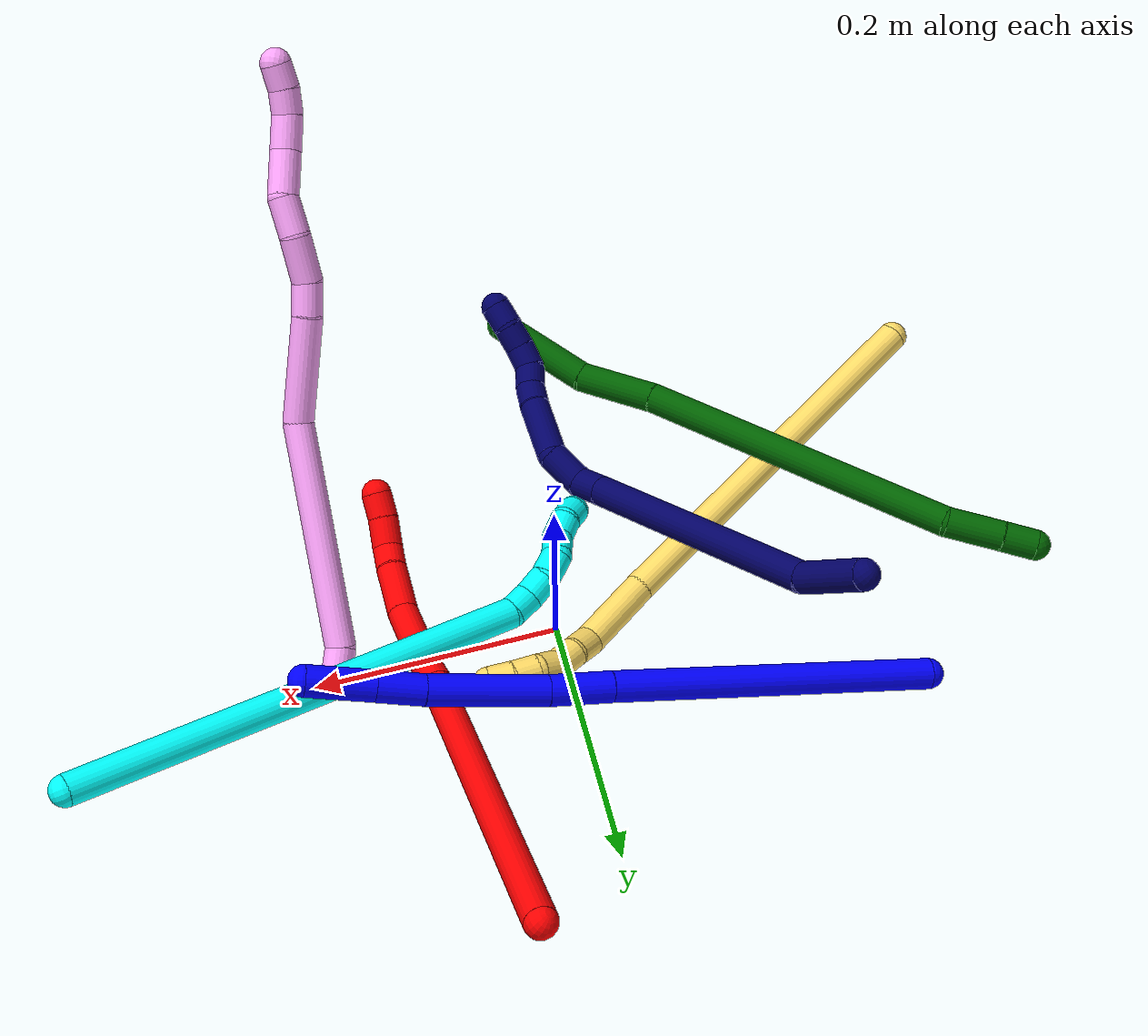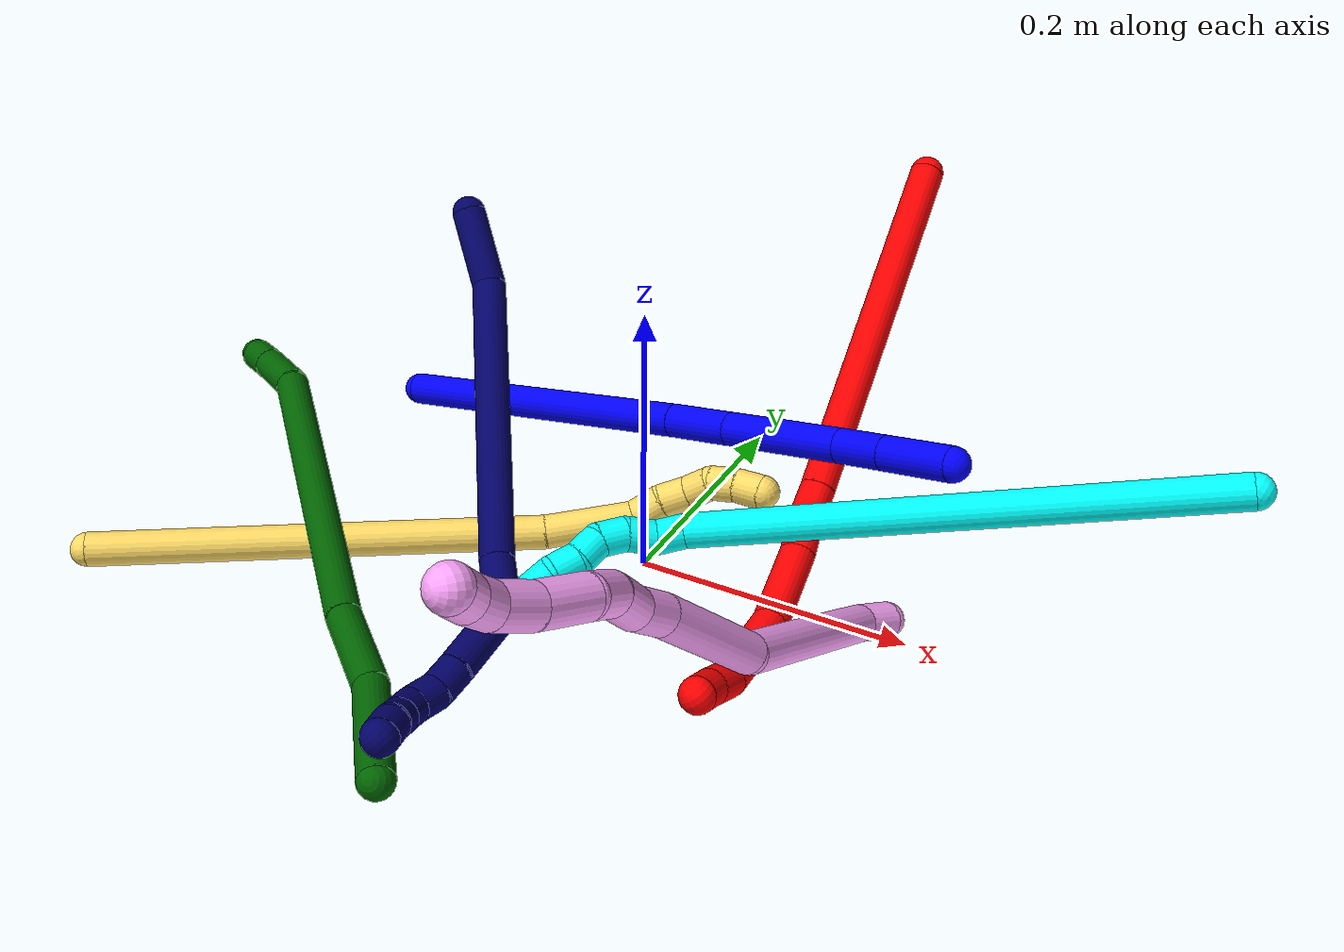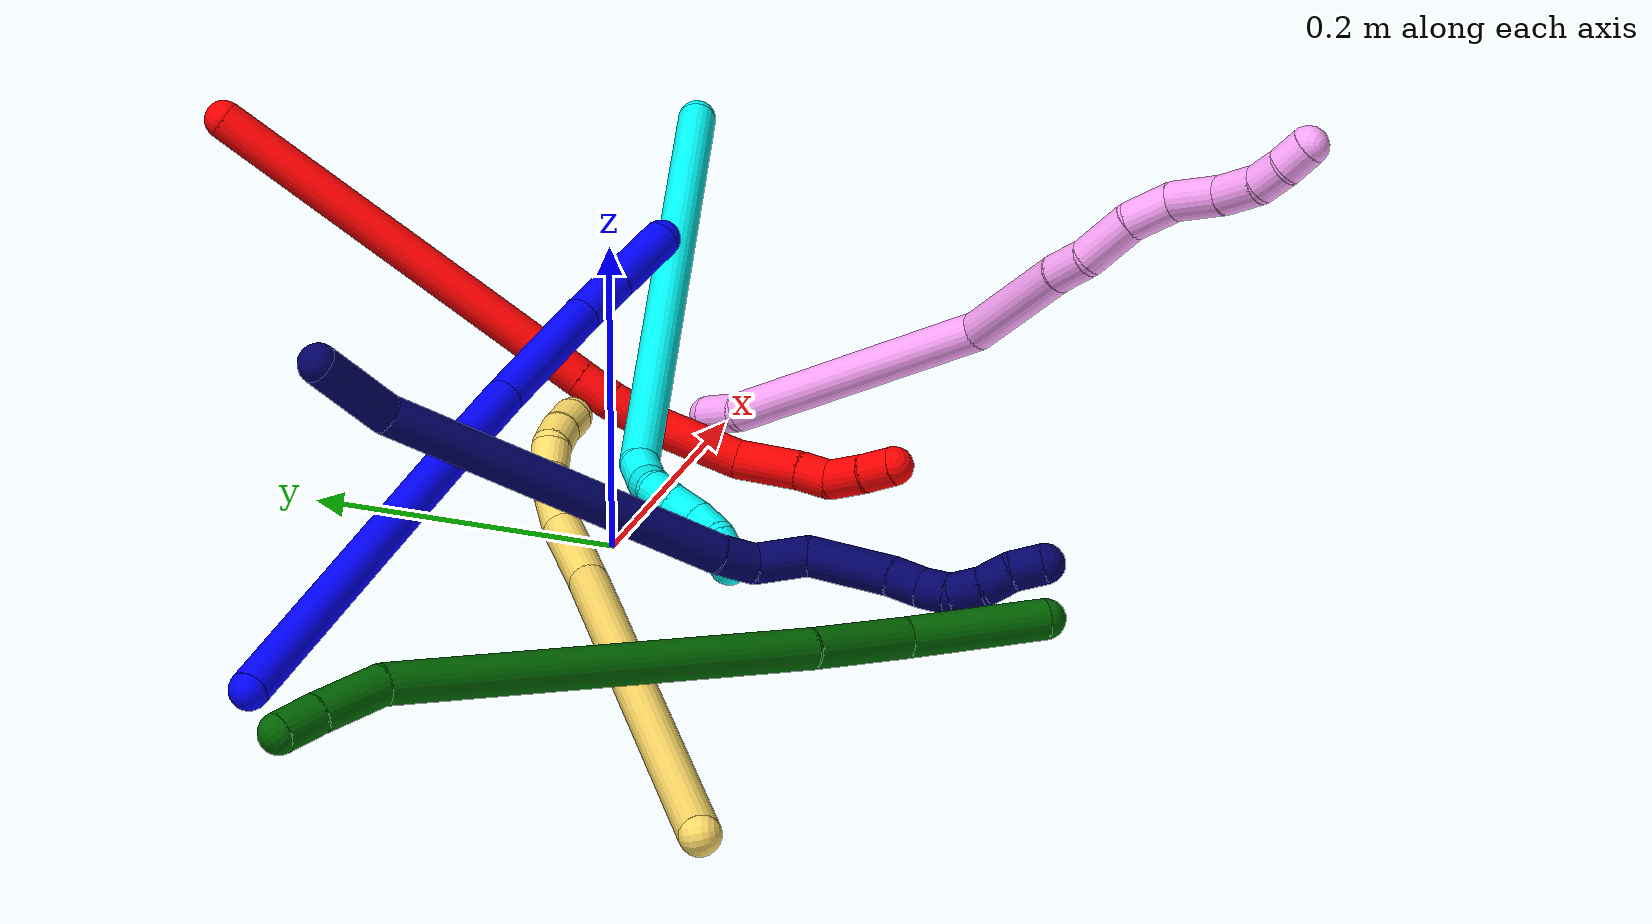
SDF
<sdf version="1.7">
 <world name="default">
  <plugin name="TubeGeneratorPlugin" filename="libtube_generator_plugin.so"/>
  <model name="photoneo_s_sensor">
   <static>1</static>
   <pose>0 0 2 1.57079 1.57079 3.14159</pose>
   <link name="link">
    <inertial><mass>0.1</mass></inertial>
    <sensor name="sensor" type="depth">
     <update_rate>30</update_rate>
     <camera>
      <horizontal_fov>1.22</horizontal_fov>
      <image><width>1920</width><height>1200</height><format>B8G8R8</format></image>
      <clip><near>0.1</near><far>4</far></clip>
      <depth_camera><output>points</output></depth_camera>
     </camera>
     <plugin name="camera_plugin" filename="libgazebo_ros_depth_camera.so">
      <baseline>0.2</baseline>
      <alwaysOn>1</alwaysOn>
      <updateRate>0.0</updateRate>
      <cameraName>camera_ir</cameraName>
      <imageTopicName>/camera/color/image_raw</imageTopicName>
      <cameraInfoTopicName>/camera/color/camera_info</cameraInfoTopicName>
      <depthImageTopicName>/camera/depth/image_raw</depthImageTopicName>
      <depthImageCameraInfoTopicName>/camera/depth/camera_info</depthImageCameraInfoTopicName>
      <pointCloudTopicName>/camera/depth/points</pointCloudTopicName>
      <frameName>fr_optical</frameName>
      <pointCloudCutoff>0.1</pointCloudCutoff>
      <pointCloudCutoffMax>2.0</pointCloudCutoffMax>
      <distortionK1>0</distortionK1>
      <distortionK2>0</distortionK2>
      <distortionK3>0</distortionK3>
      <distortionT1>0</distortionT1>
      <distortionT2>0</distortionT2>
      <CxPrime>0</CxPrime>
      <Cx>0</Cx>
      <Cy>0</Cy>
      <focalLength>0</focalLength>
      <hackBaseline>0</hackBaseline>
     </plugin>
    </sensor>
   </link>
  </model>
  <gravity>0 0 -9.8</gravity>
  <magnetic_field>6e-06 2.3e-05 -4.2e-05</magnetic_field>
  <atmosphere type="adiabatic"/>
  <physics name="default_physics" default="0" type="ode">
   <max_step_size>0.003</max_step_size>
   <real_time_factor>1</real_time_factor>
   <real_time_update_rate>1000</real_time_update_rate>
   <max_contacts>10000</max_contacts>
   <ode>
    <solver>
     <type>quick</type>
     <iters>100</iters>
     <sor>1.3</sor>
     <use_dynamic_moi_rescaling>0</use_dynamic_moi_rescaling>
    </solver>
    <constraints>
     <contact_max_correcting_vel>0</contact_max_correcting_vel>
     <contact_surface_layer>0.001</contact_surface_layer>
     <cfm>0</cfm>
     <erp>0.2</erp>
    </constraints>
   </ode>
  </physics>
  <scene><ambient>0.4 0.4 0.4 1</ambient><background>0.7 0.7 0.7 1</background><shadows>0</shadows></scene>
  <audio><device>default</device></audio>
  <spherical_coordinates>
   <surface_model>EARTH_WGS84</surface_model>
   <latitude_deg>0</latitude_deg>
   <longitude_deg>0</longitude_deg>
   <elevation>0</elevation>
   <heading_deg>0</heading_deg>
  </spherical_coordinates>
  <model name="bin">
   <static>1</static>
   <link name="bottom">
    <collision name="collision-bottom">
     <pose>0 0 -0.01 0 -0 0</pose>
     <geometry><box><size>0.8 0.6 0.02</size></box></geometry>
     <surface>
      <friction><ode><mu>100</mu><mu2>100</mu2></ode></friction>
      <contact><collide_bitmask>65535</collide_bitmask></contact>
     </surface>
    </collision>
   </link>
   <link name="west_wall">
    <collision name="collision-west_wall">
     <pose>-0.41 0 0.1 0 -0 0</pose>
     <geometry><box><size>0.02 0.6 0.2</size></box></geometry>
     <surface>
      <friction><ode><mu>100</mu><mu2>100</mu2></ode></friction>
      <contact><collide_bitmask>65535</collide_bitmask></contact>
     </surface>
    </collision>
   </link>
   <link name="east_wall">
    <collision name="collision-east_wall">
     <pose>0.41 0 0.1 0 -0 0</pose>
     <geometry><box><size>0.02 0.6 0.2</size></box></geometry>
     <surface>
      <friction><ode><mu>100</mu><mu2>100</mu2></ode></friction>
      <contact><collide_bitmask>65535</collide_bitmask></contact>
     </surface>
    </collision>
   </link>
   <link name="south_wall">
    <collision name="collision-south_wall">
     <pose>0 -0.31 0.1 0 -0 0</pose>
     <geometry><box><size>0.8 0.02 0.2</size></box></geometry>
     <surface>
      <friction><ode><mu>100</mu><mu2>100</mu2></ode></friction>
      <contact><collide_bitmask>65535</collide_bitmask></contact>
     </surface>
    </collision>
   </link>
   <link name="north_wall">
    <collision name="collision-north_wall">
     <pose>0 0.31 0.1 0 -0 0</pose>
     <geometry><box><size>0.8 0.02 0.2</size></box></geometry>
     <surface>
      <friction><ode><mu>100</mu><mu2>100</mu2></ode></friction>
      <contact><collide_bitmask>65535</collide_bitmask></contact>
     </surface>
    </collision>
   </link>
  </model>
  <model name="1">
   <static>0</static>
   <link name="1">
    <collision name="collision-cylinder-e_1_1_4">
     <pose>-0.011755 -0.026583 -0.128134 2.93703 -0.089585 -0.823479</pose>
     <geometry><cylinder><radius>0.0125</radius><length>0.262779</length></cylinder></geometry>
     <surface>
      <friction><ode><mu>1.16</mu><mu2>1.16</mu2><slip1>0</slip1><slip2>0</slip2></ode></friction>
      <contact><ode><kp>1e+06</kp><kd>1</kd><max_vel>0</max_vel><min_depth>0.001</min_depth></ode></contact>
     </surface>
    </collision>
    <visual name="visual-cylinder-e_1_1_4">
     <pose>-0.011755 -0.026583 -0.128134 2.93703 -0.089585 -0.823479</pose>
     <geometry><cylinder><radius>0.0125</radius><length>0.262779</length></cylinder></geometry>
     <material><ambient>0 0 1 1</ambient></material>
    </visual>
    <collision name="collision-cylinder-e_2_4_5">
     <pose>-0.024996 -0.058348 -0.280725 2.93281 -0.059377 -0.552398</pose>
     <geometry><cylinder><radius>0.0125</radius><length>0.050087</length></cylinder></geometry>
     <surface>
      <friction><ode><mu>1.16</mu><mu2>1.16</mu2><slip1>0</slip1><slip2>0</slip2></ode></friction>
      <contact><ode><kp>1e+06</kp><kd>1</kd><max_vel>0</max_vel><min_depth>0.001</min_depth></ode></contact>
     </surface>
    </collision>
    <visual name="visual-cylinder-e_2_4_5">
     <pose>-0.024996 -0.058348 -0.280725 2.93281 -0.059377 -0.552398</pose>
     <geometry><cylinder><radius>0.0125</radius><length>0.050087</length></cylinder></geometry>
     <material><ambient>0 0 1 1</ambient></material>
    </visual>
    <collision name="collision-cylinder-e_3_5_6">
     <pose>-0.031376 -0.071002 -0.352081 2.98359 -0.102697 -1.15158</pose>
     <geometry><cylinder><radius>0.0125</radius><length>0.095485</length></cylinder></geometry>
     <surface>
      <friction><ode><mu>1.16</mu><mu2>1.16</mu2><slip1>0</slip1><slip2>0</slip2></ode></friction>
      <contact><ode><kp>1e+06</kp><kd>1</kd><max_vel>0</max_vel><min_depth>0.001</min_depth></ode></contact>
     </surface>
    </collision>
    <visual name="visual-cylinder-e_3_5_6">
     <pose>-0.031376 -0.071002 -0.352081 2.98359 -0.102697 -1.15158</pose>
     <geometry><cylinder><radius>0.0125</radius><length>0.095485</length></cylinder></geometry>
     <material><ambient>0 0 1 1</ambient></material>
    </visual>
    <collision name="collision-cylinder-e_4_6_7">
     <pose>-0.038957 -0.080267 -0.417593 3.04558 -0.1427 -1.95797</pose>
     <geometry><cylinder><radius>0.0125</radius><length>0.037781</length></cylinder></geometry>
     <surface>
      <friction><ode><mu>1.16</mu><mu2>1.16</mu2><slip1>0</slip1><slip2>0</slip2></ode></friction>
      <contact><ode><kp>1e+06</kp><kd>1</kd><max_vel>0</max_vel><min_depth>0.001</min_depth></ode></contact>
     </surface>
    </collision>
    <visual name="visual-cylinder-e_4_6_7">
     <pose>-0.038957 -0.080267 -0.417593 3.04558 -0.1427 -1.95797</pose>
     <geometry><cylinder><radius>0.0125</radius><length>0.037781</length></cylinder></geometry>
     <material><ambient>0 0 1 1</ambient></material>
    </visual>
    <collision name="collision-cylinder-e_5_7_2">
     <pose>-0.045296 -0.084716 -0.462758 3.0419 -0.136037 -1.87739</pose>
     <geometry><cylinder><radius>0.0125</radius><length>0.053867</length></cylinder></geometry>
     <surface>
      <friction><ode><mu>1.16</mu><mu2>1.16</mu2><slip1>0</slip1><slip2>0</slip2></ode></friction>
      <contact><ode><kp>1e+06</kp><kd>1</kd><max_vel>0</max_vel><min_depth>0.001</min_depth></ode></contact>
     </surface>
    </collision>
    <visual name="visual-cylinder-e_5_7_2">
     <pose>-0.045296 -0.084716 -0.462758 3.0419 -0.136037 -1.87739</pose>
     <geometry><cylinder><radius>0.0125</radius><length>0.053867</length></cylinder></geometry>
     <material><ambient>0 0 1 1</ambient></material>
    </visual>
    <collision name="collision-sphere-2">
     <pose>-0.048949 -0.087372 -0.48931 0 -0 0</pose>
     <geometry><sphere><radius>0.0125</radius></sphere></geometry>
     <surface>
      <friction><ode><mu>1.16</mu><mu2>1.16</mu2><slip1>0</slip1><slip2>0</slip2></ode></friction>
      <contact><ode><kp>1e+06</kp><kd>1</kd><max_vel>0</max_vel><min_depth>0.001</min_depth></ode></contact>
     </surface>
    </collision>
    <visual name="visual-sphere-2">
     <pose>-0.048949 -0.087372 -0.48931 0 -0 0</pose>
     <geometry><sphere><radius>0.0125</radius></sphere></geometry>
     <material><ambient>0 0 1 1</ambient></material>
    </visual>
    <collision name="collision-sphere-7">
     <pose>-0.041644 -0.08206 -0.436205 0 -0 0</pose>
     <geometry><sphere><radius>0.0125</radius></sphere></geometry>
     <surface>
      <friction><ode><mu>1.16</mu><mu2>1.16</mu2><slip1>0</slip1><slip2>0</slip2></ode></friction>
      <contact><ode><kp>1e+06</kp><kd>1</kd><max_vel>0</max_vel><min_depth>0.001</min_depth></ode></contact>
     </surface>
    </collision>
    <visual name="visual-sphere-7">
     <pose>-0.041644 -0.08206 -0.436205 0 -0 0</pose>
     <geometry><sphere><radius>0.0125</radius></sphere></geometry>
     <material><ambient>0 0 1 1</ambient></material>
    </visual>
    <collision name="collision-sphere-6">
     <pose>-0.036271 -0.078475 -0.398981 0 -0 0</pose>
     <geometry><sphere><radius>0.0125</radius></sphere></geometry>
     <surface>
      <friction><ode><mu>1.16</mu><mu2>1.16</mu2><slip1>0</slip1><slip2>0</slip2></ode></friction>
      <contact><ode><kp>1e+06</kp><kd>1</kd><max_vel>0</max_vel><min_depth>0.001</min_depth></ode></contact>
     </surface>
    </collision>
    <visual name="visual-sphere-6">
     <pose>-0.036271 -0.078475 -0.398981 0 -0 0</pose>
     <geometry><sphere><radius>0.0125</radius></sphere></geometry>
     <material><ambient>0 0 1 1</ambient></material>
    </visual>
    <collision name="collision-sphere-5">
     <pose>-0.026482 -0.06353 -0.305182 0 -0 0</pose>
     <geometry><sphere><radius>0.0125</radius></sphere></geometry>
     <surface>
      <friction><ode><mu>1.16</mu><mu2>1.16</mu2><slip1>0</slip1><slip2>0</slip2></ode></friction>
      <contact><ode><kp>1e+06</kp><kd>1</kd><max_vel>0</max_vel><min_depth>0.001</min_depth></ode></contact>
     </surface>
    </collision>
    <visual name="visual-sphere-5">
     <pose>-0.026482 -0.06353 -0.305182 0 -0 0</pose>
     <geometry><sphere><radius>0.0125</radius></sphere></geometry>
     <material><ambient>0 0 1 1</ambient></material>
    </visual>
    <collision name="collision-sphere-1">
     <geometry><sphere><radius>0.0125</radius></sphere></geometry>
     <surface>
      <friction><ode><mu>1.16</mu><mu2>1.16</mu2><slip1>0</slip1><slip2>0</slip2></ode></friction>
      <contact><ode><kp>1e+06</kp><kd>1</kd><max_vel>0</max_vel><min_depth>0.001</min_depth></ode></contact>
     </surface>
    </collision>
    <visual name="visual-sphere-1">
     <geometry><sphere><radius>0.0125</radius></sphere></geometry>
     <material><ambient>0 0 1 1</ambient></material>
    </visual>
    <collision name="collision-sphere-4">
     <pose>-0.02351 -0.053166 -0.256269 0 -0 0</pose>
     <geometry><sphere><radius>0.0125</radius></sphere></geometry>
     <surface>
      <friction><ode><mu>1.16</mu><mu2>1.16</mu2><slip1>0</slip1><slip2>0</slip2></ode></friction>
      <contact><ode><kp>1e+06</kp><kd>1</kd><max_vel>0</max_vel><min_depth>0.001</min_depth></ode></contact>
     </surface>
    </collision>
    <visual name="visual-sphere-4">
     <pose>-0.02351 -0.053166 -0.256269 0 -0 0</pose>
     <geometry><sphere><radius>0.0125</radius></sphere></geometry>
     <material><ambient>0 0 1 1</ambient></material>
    </visual>
    <inertial>
     <pose>-0.022497 -0.048567 -0.24411 0 -0 0</pose>
     <mass>0.5</mass>
     <inertia>
      <ixx>-0.000146</ixx>
      <ixy>0</ixy>
      <ixz>0</ixz>
      <iyy>-0.00224</iyy>
      <iyz>0</iyz>
      <izz>0.000434</izz>
     </inertia>
    </inertial>
   </link>
   <pose>-0.27641 0.11965 0.011551 -1.93757 1.33032 0.907482</pose>
  </model>
  <model name="2">
   <static>0</static>
   <link name="2">
    <collision name="collision-cylinder-e_1_1_4">
     <pose>0.016635 -0.127701 0.052505 1.18071 0.119899 0.080393</pose>
     <geometry><cylinder><radius>0.0125</radius><length>0.278144</length></cylinder></geometry>
     <surface>
      <friction><ode><mu>1.16</mu><mu2>1.16</mu2><slip1>0</slip1><slip2>0</slip2></ode></friction>
      <contact><ode><kp>1e+06</kp><kd>1</kd><max_vel>0</max_vel><min_depth>0.001</min_depth></ode></contact>
     </surface>
    </collision>
    <visual name="visual-cylinder-e_1_1_4">
     <pose>0.016635 -0.127701 0.052505 1.18071 0.119899 0.080393</pose>
     <geometry><cylinder><radius>0.0125</radius><length>0.278144</length></cylinder></geometry>
     <material><ambient>1 0 0 1</ambient></material>
    </visual>
    <collision name="collision-cylinder-e_2_4_5">
     <pose>0.034819 -0.266305 0.109156 1.20752 0.13209 0.091168</pose>
     <geometry><cylinder><radius>0.0125</radius><length>0.023534</length></cylinder></geometry>
     <surface>
      <friction><ode><mu>1.16</mu><mu2>1.16</mu2><slip1>0</slip1><slip2>0</slip2></ode></friction>
      <contact><ode><kp>1e+06</kp><kd>1</kd><max_vel>0</max_vel><min_depth>0.001</min_depth></ode></contact>
     </surface>
    </collision>
    <visual name="visual-cylinder-e_2_4_5">
     <pose>0.034819 -0.266305 0.109156 1.20752 0.13209 0.091168</pose>
     <geometry><cylinder><radius>0.0125</radius><length>0.023534</length></cylinder></geometry>
     <material><ambient>1 0 0 1</ambient></material>
    </visual>
    <collision name="collision-cylinder-e_3_5_6">
     <pose>0.036318 -0.290773 0.118828 1.18388 -0.003503 -0.002355</pose>
     <geometry><cylinder><radius>0.0125</radius><length>0.029296</length></cylinder></geometry>
     <surface>
      <friction><ode><mu>1.16</mu><mu2>1.16</mu2><slip1>0</slip1><slip2>0</slip2></ode></friction>
      <contact><ode><kp>1e+06</kp><kd>1</kd><max_vel>0</max_vel><min_depth>0.001</min_depth></ode></contact>
     </surface>
    </collision>
    <visual name="visual-cylinder-e_3_5_6">
     <pose>0.036318 -0.290773 0.118828 1.18388 -0.003503 -0.002355</pose>
     <geometry><cylinder><radius>0.0125</radius><length>0.029296</length></cylinder></geometry>
     <material><ambient>1 0 0 1</ambient></material>
    </visual>
    <collision name="collision-cylinder-e_4_6_7">
     <pose>0.034614 -0.333926 0.130583 1.36332 -0.054588 -0.044297</pose>
     <geometry><cylinder><radius>0.0125</radius><length>0.060562</length></cylinder></geometry>
     <surface>
      <friction><ode><mu>1.16</mu><mu2>1.16</mu2><slip1>0</slip1><slip2>0</slip2></ode></friction>
      <contact><ode><kp>1e+06</kp><kd>1</kd><max_vel>0</max_vel><min_depth>0.001</min_depth></ode></contact>
     </surface>
    </collision>
    <visual name="visual-cylinder-e_4_6_7">
     <pose>0.034614 -0.333926 0.130583 1.36332 -0.054588 -0.044297</pose>
     <geometry><cylinder><radius>0.0125</radius><length>0.060562</length></cylinder></geometry>
     <material><ambient>1 0 0 1</ambient></material>
    </visual>
    <collision name="collision-cylinder-e_5_7_8">
     <pose>0.030027 -0.384015 0.13504 1.657 -0.141696 -0.15442</pose>
     <geometry><cylinder><radius>0.0125</radius><length>0.041571</length></cylinder></geometry>
     <surface>
      <friction><ode><mu>1.16</mu><mu2>1.16</mu2><slip1>0</slip1><slip2>0</slip2></ode></friction>
      <contact><ode><kp>1e+06</kp><kd>1</kd><max_vel>0</max_vel><min_depth>0.001</min_depth></ode></contact>
     </surface>
    </collision>
    <visual name="visual-cylinder-e_5_7_8">
     <pose>0.030027 -0.384015 0.13504 1.657 -0.141696 -0.15442</pose>
     <geometry><cylinder><radius>0.0125</radius><length>0.041571</length></cylinder></geometry>
     <material><ambient>1 0 0 1</ambient></material>
    </visual>
    <collision name="collision-cylinder-e_6_8_9">
     <pose>0.026669 -0.414853 0.13285 1.61127 -0.040823 -0.042509</pose>
     <geometry><cylinder><radius>0.0125</radius><length>0.020711</length></cylinder></geometry>
     <surface>
      <friction><ode><mu>1.16</mu><mu2>1.16</mu2><slip1>0</slip1><slip2>0</slip2></ode></friction>
      <contact><ode><kp>1e+06</kp><kd>1</kd><max_vel>0</max_vel><min_depth>0.001</min_depth></ode></contact>
     </surface>
    </collision>
    <visual name="visual-cylinder-e_6_8_9">
     <pose>0.026669 -0.414853 0.13285 1.61127 -0.040823 -0.042509</pose>
     <geometry><cylinder><radius>0.0125</radius><length>0.020711</length></cylinder></geometry>
     <material><ambient>1 0 0 1</ambient></material>
    </visual>
    <collision name="collision-cylinder-e_7_9_10">
     <pose>0.022652 -0.436079 0.126848 2.04471 -0.285711 -0.462429</pose>
     <geometry><cylinder><radius>0.0125</radius><length>0.025505</length></cylinder></geometry>
     <surface>
      <friction><ode><mu>1.16</mu><mu2>1.16</mu2><slip1>0</slip1><slip2>0</slip2></ode></friction>
      <contact><ode><kp>1e+06</kp><kd>1</kd><max_vel>0</max_vel><min_depth>0.001</min_depth></ode></contact>
     </surface>
    </collision>
    <visual name="visual-cylinder-e_7_9_10">
     <pose>0.022652 -0.436079 0.126848 2.04471 -0.285711 -0.462429</pose>
     <geometry><cylinder><radius>0.0125</radius><length>0.025505</length></cylinder></geometry>
     <material><ambient>1 0 0 1</ambient></material>
    </visual>
    <collision name="collision-cylinder-e_8_10_2">
     <pose>0.015023 -0.455563 0.117178 2.0144 -0.400931 -0.622169</pose>
     <geometry><cylinder><radius>0.0125</radius><length>0.020677</length></cylinder></geometry>
     <surface>
      <friction><ode><mu>1.16</mu><mu2>1.16</mu2><slip1>0</slip1><slip2>0</slip2></ode></friction>
      <contact><ode><kp>1e+06</kp><kd>1</kd><max_vel>0</max_vel><min_depth>0.001</min_depth></ode></contact>
     </surface>
    </collision>
    <visual name="visual-cylinder-e_8_10_2">
     <pose>0.015023 -0.455563 0.117178 2.0144 -0.400931 -0.622169</pose>
     <geometry><cylinder><radius>0.0125</radius><length>0.020677</length></cylinder></geometry>
     <material><ambient>1 0 0 1</ambient></material>
    </visual>
    <collision name="collision-sphere-2">
     <pose>0.010988 -0.46416 0.113093 0 -0 0</pose>
     <geometry><sphere><radius>0.0125</radius></sphere></geometry>
     <surface>
      <friction><ode><mu>1.16</mu><mu2>1.16</mu2><slip1>0</slip1><slip2>0</slip2></ode></friction>
      <contact><ode><kp>1e+06</kp><kd>1</kd><max_vel>0</max_vel><min_depth>0.001</min_depth></ode></contact>
     </surface>
    </collision>
    <visual name="visual-sphere-2">
     <pose>0.010988 -0.46416 0.113093 0 -0 0</pose>
     <geometry><sphere><radius>0.0125</radius></sphere></geometry>
     <material><ambient>1 0 0 1</ambient></material>
    </visual>
    <collision name="collision-sphere-10">
     <pose>0.019058 -0.446965 0.121264 0 -0 0</pose>
     <geometry><sphere><radius>0.0125</radius></sphere></geometry>
     <surface>
      <friction><ode><mu>1.16</mu><mu2>1.16</mu2><slip1>0</slip1><slip2>0</slip2></ode></friction>
      <contact><ode><kp>1e+06</kp><kd>1</kd><max_vel>0</max_vel><min_depth>0.001</min_depth></ode></contact>
     </surface>
    </collision>
    <visual name="visual-sphere-10">
     <pose>0.019058 -0.446965 0.121264 0 -0 0</pose>
     <geometry><sphere><radius>0.0125</radius></sphere></geometry>
     <material><ambient>1 0 0 1</ambient></material>
    </visual>
    <collision name="collision-sphere-9">
     <pose>0.026246 -0.425192 0.132431 0 -0 0</pose>
     <geometry><sphere><radius>0.0125</radius></sphere></geometry>
     <surface>
      <friction><ode><mu>1.16</mu><mu2>1.16</mu2><slip1>0</slip1><slip2>0</slip2></ode></friction>
      <contact><ode><kp>1e+06</kp><kd>1</kd><max_vel>0</max_vel><min_depth>0.001</min_depth></ode></contact>
     </surface>
    </collision>
    <visual name="visual-sphere-9">
     <pose>0.026246 -0.425192 0.132431 0 -0 0</pose>
     <geometry><sphere><radius>0.0125</radius></sphere></geometry>
     <material><ambient>1 0 0 1</ambient></material>
    </visual>
    <collision name="collision-sphere-4">
     <pose>0.033269 -0.255401 0.105011 0 -0 0</pose>
     <geometry><sphere><radius>0.0125</radius></sphere></geometry>
     <surface>
      <friction><ode><mu>1.16</mu><mu2>1.16</mu2><slip1>0</slip1><slip2>0</slip2></ode></friction>
      <contact><ode><kp>1e+06</kp><kd>1</kd><max_vel>0</max_vel><min_depth>0.001</min_depth></ode></contact>
     </surface>
    </collision>
    <visual name="visual-sphere-4">
     <pose>0.033269 -0.255401 0.105011 0 -0 0</pose>
     <geometry><sphere><radius>0.0125</radius></sphere></geometry>
     <material><ambient>1 0 0 1</ambient></material>
    </visual>
    <collision name="collision-sphere-1">
     <geometry><sphere><radius>0.0125</radius></sphere></geometry>
     <surface>
      <friction><ode><mu>1.16</mu><mu2>1.16</mu2><slip1>0</slip1><slip2>0</slip2></ode></friction>
      <contact><ode><kp>1e+06</kp><kd>1</kd><max_vel>0</max_vel><min_depth>0.001</min_depth></ode></contact>
     </surface>
    </collision>
    <visual name="visual-sphere-1">
     <geometry><sphere><radius>0.0125</radius></sphere></geometry>
     <material><ambient>1 0 0 1</ambient></material>
    </visual>
    <collision name="collision-sphere-8">
     <pose>0.027091 -0.404515 0.133269 0 -0 0</pose>
     <geometry><sphere><radius>0.0125</radius></sphere></geometry>
     <surface>
      <friction><ode><mu>1.16</mu><mu2>1.16</mu2><slip1>0</slip1><slip2>0</slip2></ode></friction>
      <contact><ode><kp>1e+06</kp><kd>1</kd><max_vel>0</max_vel><min_depth>0.001</min_depth></ode></contact>
     </surface>
    </collision>
    <visual name="visual-sphere-8">
     <pose>0.027091 -0.404515 0.133269 0 -0 0</pose>
     <geometry><sphere><radius>0.0125</radius></sphere></geometry>
     <material><ambient>1 0 0 1</ambient></material>
    </visual>
    <collision name="collision-sphere-5">
     <pose>0.036369 -0.277208 0.1133 0 -0 0</pose>
     <geometry><sphere><radius>0.0125</radius></sphere></geometry>
     <surface>
      <friction><ode><mu>1.16</mu><mu2>1.16</mu2><slip1>0</slip1><slip2>0</slip2></ode></friction>
      <contact><ode><kp>1e+06</kp><kd>1</kd><max_vel>0</max_vel><min_depth>0.001</min_depth></ode></contact>
     </surface>
    </collision>
    <visual name="visual-sphere-5">
     <pose>0.036369 -0.277208 0.1133 0 -0 0</pose>
     <geometry><sphere><radius>0.0125</radius></sphere></geometry>
     <material><ambient>1 0 0 1</ambient></material>
    </visual>
    <collision name="collision-sphere-6">
     <pose>0.036266 -0.304339 0.124355 0 -0 0</pose>
     <geometry><sphere><radius>0.0125</radius></sphere></geometry>
     <surface>
      <friction><ode><mu>1.16</mu><mu2>1.16</mu2><slip1>0</slip1><slip2>0</slip2></ode></friction>
      <contact><ode><kp>1e+06</kp><kd>1</kd><max_vel>0</max_vel><min_depth>0.001</min_depth></ode></contact>
     </surface>
    </collision>
    <visual name="visual-sphere-6">
     <pose>0.036266 -0.304339 0.124355 0 -0 0</pose>
     <geometry><sphere><radius>0.0125</radius></sphere></geometry>
     <material><ambient>1 0 0 1</ambient></material>
    </visual>
    <collision name="collision-sphere-7">
     <pose>0.032962 -0.363514 0.136812 0 -0 0</pose>
     <geometry><sphere><radius>0.0125</radius></sphere></geometry>
     <surface>
      <friction><ode><mu>1.16</mu><mu2>1.16</mu2><slip1>0</slip1><slip2>0</slip2></ode></friction>
      <contact><ode><kp>1e+06</kp><kd>1</kd><max_vel>0</max_vel><min_depth>0.001</min_depth></ode></contact>
     </surface>
    </collision>
    <visual name="visual-sphere-7">
     <pose>0.032962 -0.363514 0.136812 0 -0 0</pose>
     <geometry><sphere><radius>0.0125</radius></sphere></geometry>
     <material><ambient>1 0 0 1</ambient></material>
    </visual>
    <inertial>
     <pose>0.022591 -0.231252 0.085172 0 -0 0</pose>
     <mass>0.5</mass>
     <inertia>
      <ixx>0.001964</ixx>
      <ixy>0</ixy>
      <ixz>0</ixz>
      <iyy>0.000808</iyy>
      <iyz>0</iyz>
      <izz>0.001491</izz>
     </inertia>
    </inertial>
   </link>
   <pose>0.087902 0.295866 0.211857 2.91501 0.598221 2.94667</pose>
  </model>
  <model name="3">
   <static>0</static>
   <link name="3">
    <collision name="collision-cylinder-e_1_1_4">
     <pose>-0.047578 -0.098538 -0.152987 2.56938 -0.255732 -0.824051</pose>
     <geometry><cylinder><radius>0.0125</radius><length>0.376183</length></cylinder></geometry>
     <surface>
      <friction><ode><mu>1.16</mu><mu2>1.16</mu2><slip1>0</slip1><slip2>0</slip2></ode></friction>
      <contact><ode><kp>1e+06</kp><kd>1</kd><max_vel>0</max_vel><min_depth>0.001</min_depth></ode></contact>
     </surface>
    </collision>
    <visual name="visual-cylinder-e_1_1_4">
     <pose>-0.047578 -0.098538 -0.152987 2.56938 -0.255732 -0.824051</pose>
     <geometry><cylinder><radius>0.0125</radius><length>0.376183</length></cylinder></geometry>
     <material><ambient>0.003922 1 0.996078 1</ambient></material>
    </visual>
    <collision name="collision-cylinder-e_2_4_5">
     <pose>-0.101252 -0.201868 -0.313394 2.56816 -0.603995 -1.62582</pose>
     <geometry><cylinder><radius>0.0125</radius><length>0.021462</length></cylinder></geometry>
     <surface>
      <friction><ode><mu>1.16</mu><mu2>1.16</mu2><slip1>0</slip1><slip2>0</slip2></ode></friction>
      <contact><ode><kp>1e+06</kp><kd>1</kd><max_vel>0</max_vel><min_depth>0.001</min_depth></ode></contact>
     </surface>
    </collision>
    <visual name="visual-cylinder-e_2_4_5">
     <pose>-0.101252 -0.201868 -0.313394 2.56816 -0.603995 -1.62582</pose>
     <geometry><cylinder><radius>0.0125</radius><length>0.021462</length></cylinder></geometry>
     <material><ambient>0.003922 1 0.996078 1</ambient></material>
    </visual>
    <collision name="collision-cylinder-e_3_5_6">
     <pose>-0.113218 -0.207144 -0.329714 3.08717 -0.582486 -2.96049</pose>
     <geometry><cylinder><radius>0.0125</radius><length>0.021348</length></cylinder></geometry>
     <surface>
      <friction><ode><mu>1.16</mu><mu2>1.16</mu2><slip1>0</slip1><slip2>0</slip2></ode></friction>
      <contact><ode><kp>1e+06</kp><kd>1</kd><max_vel>0</max_vel><min_depth>0.001</min_depth></ode></contact>
     </surface>
    </collision>
    <visual name="visual-cylinder-e_3_5_6">
     <pose>-0.113218 -0.207144 -0.329714 3.08717 -0.582486 -2.96049</pose>
     <geometry><cylinder><radius>0.0125</radius><length>0.021348</length></cylinder></geometry>
     <material><ambient>0.003922 1 0.996078 1</ambient></material>
    </visual>
    <collision name="collision-cylinder-e_4_6_7">
     <pose>-0.127014 -0.210012 -0.344827 2.77541 -0.872324 -2.3853</pose>
     <geometry><cylinder><radius>0.0125</radius><length>0.020694</length></cylinder></geometry>
     <surface>
      <friction><ode><mu>1.16</mu><mu2>1.16</mu2><slip1>0</slip1><slip2>0</slip2></ode></friction>
      <contact><ode><kp>1e+06</kp><kd>1</kd><max_vel>0</max_vel><min_depth>0.001</min_depth></ode></contact>
     </surface>
    </collision>
    <visual name="visual-cylinder-e_4_6_7">
     <pose>-0.127014 -0.210012 -0.344827 2.77541 -0.872324 -2.3853</pose>
     <geometry><cylinder><radius>0.0125</radius><length>0.020694</length></cylinder></geometry>
     <material><ambient>0.003922 1 0.996078 1</ambient></material>
    </visual>
    <collision name="collision-cylinder-e_5_7_8">
     <pose>-0.144219 -0.216257 -0.352419 1.91376 -1.15464 -1.49205</pose>
     <geometry><cylinder><radius>0.0125</radius><length>0.020296</length></cylinder></geometry>
     <surface>
      <friction><ode><mu>1.16</mu><mu2>1.16</mu2><slip1>0</slip1><slip2>0</slip2></ode></friction>
      <contact><ode><kp>1e+06</kp><kd>1</kd><max_vel>0</max_vel><min_depth>0.001</min_depth></ode></contact>
     </surface>
    </collision>
    <visual name="visual-cylinder-e_5_7_8">
     <pose>-0.144219 -0.216257 -0.352419 1.91376 -1.15464 -1.49205</pose>
     <geometry><cylinder><radius>0.0125</radius><length>0.020296</length></cylinder></geometry>
     <material><ambient>0.003922 1 0.996078 1</ambient></material>
    </visual>
    <collision name="collision-cylinder-e_6_8_9">
     <pose>-0.161603 -0.224115 -0.358107 2.39401 -0.943331 -1.83051</pose>
     <geometry><cylinder><radius>0.0125</radius><length>0.020017</length></cylinder></geometry>
     <surface>
      <friction><ode><mu>1.16</mu><mu2>1.16</mu2><slip1>0</slip1><slip2>0</slip2></ode></friction>
      <contact><ode><kp>1e+06</kp><kd>1</kd><max_vel>0</max_vel><min_depth>0.001</min_depth></ode></contact>
     </surface>
    </collision>
    <visual name="visual-cylinder-e_6_8_9">
     <pose>-0.161603 -0.224115 -0.358107 2.39401 -0.943331 -1.83051</pose>
     <geometry><cylinder><radius>0.0125</radius><length>0.020017</length></cylinder></geometry>
     <material><ambient>0.003922 1 0.996078 1</ambient></material>
    </visual>
    <collision name="collision-cylinder-e_7_9_2">
     <pose>-0.176057 -0.235146 -0.365603 1.99606 -0.688301 -1.01455</pose>
     <geometry><cylinder><radius>0.0125</radius><length>0.02</length></cylinder></geometry>
     <surface>
      <friction><ode><mu>1.16</mu><mu2>1.16</mu2><slip1>0</slip1><slip2>0</slip2></ode></friction>
      <contact><ode><kp>1e+06</kp><kd>1</kd><max_vel>0</max_vel><min_depth>0.001</min_depth></ode></contact>
     </surface>
    </collision>
    <visual name="visual-cylinder-e_7_9_2">
     <pose>-0.176057 -0.235146 -0.365603 1.99606 -0.688301 -1.01455</pose>
     <geometry><cylinder><radius>0.0125</radius><length>0.02</length></cylinder></geometry>
     <material><ambient>0.003922 1 0.996078 1</ambient></material>
    </visual>
    <collision name="collision-sphere-2">
     <pose>-0.18241 -0.242181 -0.368789 0 -0 0</pose>
     <geometry><sphere><radius>0.0125</radius></sphere></geometry>
     <surface>
      <friction><ode><mu>1.16</mu><mu2>1.16</mu2><slip1>0</slip1><slip2>0</slip2></ode></friction>
      <contact><ode><kp>1e+06</kp><kd>1</kd><max_vel>0</max_vel><min_depth>0.001</min_depth></ode></contact>
     </surface>
    </collision>
    <visual name="visual-sphere-2">
     <pose>-0.18241 -0.242181 -0.368789 0 -0 0</pose>
     <geometry><sphere><radius>0.0125</radius></sphere></geometry>
     <material><ambient>0.003922 1 0.996078 1</ambient></material>
    </visual>
    <collision name="collision-sphere-9">
     <pose>-0.169705 -0.22811 -0.362417 0 -0 0</pose>
     <geometry><sphere><radius>0.0125</radius></sphere></geometry>
     <surface>
      <friction><ode><mu>1.16</mu><mu2>1.16</mu2><slip1>0</slip1><slip2>0</slip2></ode></friction>
      <contact><ode><kp>1e+06</kp><kd>1</kd><max_vel>0</max_vel><min_depth>0.001</min_depth></ode></contact>
     </surface>
    </collision>
    <visual name="visual-sphere-9">
     <pose>-0.169705 -0.22811 -0.362417 0 -0 0</pose>
     <geometry><sphere><radius>0.0125</radius></sphere></geometry>
     <material><ambient>0.003922 1 0.996078 1</ambient></material>
    </visual>
    <collision name="collision-sphere-4">
     <pose>-0.095157 -0.197076 -0.305974 0 -0 0</pose>
     <geometry><sphere><radius>0.0125</radius></sphere></geometry>
     <surface>
      <friction><ode><mu>1.16</mu><mu2>1.16</mu2><slip1>0</slip1><slip2>0</slip2></ode></friction>
      <contact><ode><kp>1e+06</kp><kd>1</kd><max_vel>0</max_vel><min_depth>0.001</min_depth></ode></contact>
     </surface>
    </collision>
    <visual name="visual-sphere-4">
     <pose>-0.095157 -0.197076 -0.305974 0 -0 0</pose>
     <geometry><sphere><radius>0.0125</radius></sphere></geometry>
     <material><ambient>0.003922 1 0.996078 1</ambient></material>
    </visual>
    <collision name="collision-sphere-1">
     <geometry><sphere><radius>0.0125</radius></sphere></geometry>
     <surface>
      <friction><ode><mu>1.16</mu><mu2>1.16</mu2><slip1>0</slip1><slip2>0</slip2></ode></friction>
      <contact><ode><kp>1e+06</kp><kd>1</kd><max_vel>0</max_vel><min_depth>0.001</min_depth></ode></contact>
     </surface>
    </collision>
    <visual name="visual-sphere-1">
     <geometry><sphere><radius>0.0125</radius></sphere></geometry>
     <material><ambient>0.003922 1 0.996078 1</ambient></material>
    </visual>
    <collision name="collision-sphere-8">
     <pose>-0.153501 -0.220121 -0.353798 0 -0 0</pose>
     <geometry><sphere><radius>0.0125</radius></sphere></geometry>
     <surface>
      <friction><ode><mu>1.16</mu><mu2>1.16</mu2><slip1>0</slip1><slip2>0</slip2></ode></friction>
      <contact><ode><kp>1e+06</kp><kd>1</kd><max_vel>0</max_vel><min_depth>0.001</min_depth></ode></contact>
     </surface>
    </collision>
    <visual name="visual-sphere-8">
     <pose>-0.153501 -0.220121 -0.353798 0 -0 0</pose>
     <geometry><sphere><radius>0.0125</radius></sphere></geometry>
     <material><ambient>0.003922 1 0.996078 1</ambient></material>
    </visual>
    <collision name="collision-sphere-5">
     <pose>-0.107346 -0.206659 -0.320813 0 -0 0</pose>
     <geometry><sphere><radius>0.0125</radius></sphere></geometry>
     <surface>
      <friction><ode><mu>1.16</mu><mu2>1.16</mu2><slip1>0</slip1><slip2>0</slip2></ode></friction>
      <contact><ode><kp>1e+06</kp><kd>1</kd><max_vel>0</max_vel><min_depth>0.001</min_depth></ode></contact>
     </surface>
    </collision>
    <visual name="visual-sphere-5">
     <pose>-0.107346 -0.206659 -0.320813 0 -0 0</pose>
     <geometry><sphere><radius>0.0125</radius></sphere></geometry>
     <material><ambient>0.003922 1 0.996078 1</ambient></material>
    </visual>
    <collision name="collision-sphere-6">
     <pose>-0.11909 -0.207629 -0.338615 0 -0 0</pose>
     <geometry><sphere><radius>0.0125</radius></sphere></geometry>
     <surface>
      <friction><ode><mu>1.16</mu><mu2>1.16</mu2><slip1>0</slip1><slip2>0</slip2></ode></friction>
      <contact><ode><kp>1e+06</kp><kd>1</kd><max_vel>0</max_vel><min_depth>0.001</min_depth></ode></contact>
     </surface>
    </collision>
    <visual name="visual-sphere-6">
     <pose>-0.11909 -0.207629 -0.338615 0 -0 0</pose>
     <geometry><sphere><radius>0.0125</radius></sphere></geometry>
     <material><ambient>0.003922 1 0.996078 1</ambient></material>
    </visual>
    <collision name="collision-sphere-7">
     <pose>-0.134937 -0.212394 -0.351039 0 -0 0</pose>
     <geometry><sphere><radius>0.0125</radius></sphere></geometry>
     <surface>
      <friction><ode><mu>1.16</mu><mu2>1.16</mu2><slip1>0</slip1><slip2>0</slip2></ode></friction>
      <contact><ode><kp>1e+06</kp><kd>1</kd><max_vel>0</max_vel><min_depth>0.001</min_depth></ode></contact>
     </surface>
    </collision>
    <visual name="visual-sphere-7">
     <pose>-0.134937 -0.212394 -0.351039 0 -0 0</pose>
     <geometry><sphere><radius>0.0125</radius></sphere></geometry>
     <material><ambient>0.003922 1 0.996078 1</ambient></material>
    </visual>
    <inertial>
     <pose>-0.069599 -0.127494 -0.200169 0 -0 0</pose>
     <mass>0.5</mass>
     <inertia>
      <ixx>-0.000256</ixx>
      <ixy>0</ixy>
      <ixz>0</ixz>
      <iyy>-0.005272</iyy>
      <iyz>0</iyz>
      <izz>0.003439</izz>
     </inertia>
    </inertial>
   </link>
   <pose>0.388479 0.089213 0.130653 1.89542 0.00991 1.56439</pose>
  </model>
  <model name="4">
   <static>0</static>
   <link name="4">
    <collision name="collision-cylinder-e_1_1_4">
     <pose>0.000362 -0.000905 0.014171 0.063801 0.02546 0.000813</pose>
     <geometry><cylinder><radius>0.0125</radius><length>0.028409</length></cylinder></geometry>
     <surface>
      <friction><ode><mu>1.16</mu><mu2>1.16</mu2><slip1>0</slip1><slip2>0</slip2></ode></friction>
      <contact><ode><kp>1e+06</kp><kd>1</kd><max_vel>0</max_vel><min_depth>0.001</min_depth></ode></contact>
     </surface>
    </collision>
    <visual name="visual-cylinder-e_1_1_4">
     <pose>0.000362 -0.000905 0.014171 0.063801 0.02546 0.000813</pose>
     <geometry><cylinder><radius>0.0125</radius><length>0.028409</length></cylinder></geometry>
     <material><ambient>1 0.65098 0.996078 1</ambient></material>
    </visual>
    <collision name="collision-cylinder-e_2_4_5">
     <pose>-0.005849 -0.0361 0.112977 0.384931 -0.07185 -0.014008</pose>
     <geometry><cylinder><radius>0.0125</radius><length>0.183106</length></cylinder></geometry>
     <surface>
      <friction><ode><mu>1.16</mu><mu2>1.16</mu2><slip1>0</slip1><slip2>0</slip2></ode></friction>
      <contact><ode><kp>1e+06</kp><kd>1</kd><max_vel>0</max_vel><min_depth>0.001</min_depth></ode></contact>
     </surface>
    </collision>
    <visual name="visual-cylinder-e_2_4_5">
     <pose>-0.005849 -0.0361 0.112977 0.384931 -0.07185 -0.014008</pose>
     <geometry><cylinder><radius>0.0125</radius><length>0.183106</length></cylinder></geometry>
     <material><ambient>1 0.65098 0.996078 1</ambient></material>
    </visual>
    <collision name="collision-cylinder-e_3_5_6">
     <pose>0.000609 -0.082749 0.236797 0.305542 0.307107 0.047652</pose>
     <geometry><cylinder><radius>0.0125</radius><length>0.086211</length></cylinder></geometry>
     <surface>
      <friction><ode><mu>1.16</mu><mu2>1.16</mu2><slip1>0</slip1><slip2>0</slip2></ode></friction>
      <contact><ode><kp>1e+06</kp><kd>1</kd><max_vel>0</max_vel><min_depth>0.001</min_depth></ode></contact>
     </surface>
    </collision>
    <visual name="visual-cylinder-e_3_5_6">
     <pose>0.000609 -0.082749 0.236797 0.305542 0.307107 0.047652</pose>
     <geometry><cylinder><radius>0.0125</radius><length>0.086211</length></cylinder></geometry>
     <material><ambient>1 0.65098 0.996078 1</ambient></material>
    </visual>
    <collision name="collision-cylinder-e_4_6_7">
     <pose>0.015952 -0.099254 0.288621 0.316971 0.172113 0.027575</pose>
     <geometry><cylinder><radius>0.0125</radius><length>0.027</length></cylinder></geometry>
     <surface>
      <friction><ode><mu>1.16</mu><mu2>1.16</mu2><slip1>0</slip1><slip2>0</slip2></ode></friction>
      <contact><ode><kp>1e+06</kp><kd>1</kd><max_vel>0</max_vel><min_depth>0.001</min_depth></ode></contact>
     </surface>
    </collision>
    <visual name="visual-cylinder-e_4_6_7">
     <pose>0.015952 -0.099254 0.288621 0.316971 0.172113 0.027575</pose>
     <geometry><cylinder><radius>0.0125</radius><length>0.027</length></cylinder></geometry>
     <material><ambient>1 0.65098 0.996078 1</ambient></material>
    </visual>
    <collision name="collision-cylinder-e_5_7_8">
     <pose>0.021067 -0.114266 0.316416 0.622003 0.14919 0.048034</pose>
     <geometry><cylinder><radius>0.0125</radius><length>0.037718</length></cylinder></geometry>
     <surface>
      <friction><ode><mu>1.16</mu><mu2>1.16</mu2><slip1>0</slip1><slip2>0</slip2></ode></friction>
      <contact><ode><kp>1e+06</kp><kd>1</kd><max_vel>0</max_vel><min_depth>0.001</min_depth></ode></contact>
     </surface>
    </collision>
    <visual name="visual-cylinder-e_5_7_8">
     <pose>0.021067 -0.114266 0.316416 0.622003 0.14919 0.048034</pose>
     <geometry><cylinder><radius>0.0125</radius><length>0.037718</length></cylinder></geometry>
     <material><ambient>1 0.65098 0.996078 1</ambient></material>
    </visual>
    <collision name="collision-cylinder-e_6_8_9">
     <pose>0.022818 -0.132811 0.344984 0.519976 -0.068005 -0.018097</pose>
     <geometry><cylinder><radius>0.0125</radius><length>0.03098</length></cylinder></geometry>
     <surface>
      <friction><ode><mu>1.16</mu><mu2>1.16</mu2><slip1>0</slip1><slip2>0</slip2></ode></friction>
      <contact><ode><kp>1e+06</kp><kd>1</kd><max_vel>0</max_vel><min_depth>0.001</min_depth></ode></contact>
     </surface>
    </collision>
    <visual name="visual-cylinder-e_6_8_9">
     <pose>0.022818 -0.132811 0.344984 0.519976 -0.068005 -0.018097</pose>
     <geometry><cylinder><radius>0.0125</radius><length>0.03098</length></cylinder></geometry>
     <material><ambient>1 0.65098 0.996078 1</ambient></material>
    </visual>
    <collision name="collision-cylinder-e_7_9_10">
     <pose>0.020846 -0.142796 0.376652 0.12567 -0.049928 -0.003142</pose>
     <geometry><cylinder><radius>0.0125</radius><length>0.03685</length></cylinder></geometry>
     <surface>
      <friction><ode><mu>1.16</mu><mu2>1.16</mu2><slip1>0</slip1><slip2>0</slip2></ode></friction>
      <contact><ode><kp>1e+06</kp><kd>1</kd><max_vel>0</max_vel><min_depth>0.001</min_depth></ode></contact>
     </surface>
    </collision>
    <visual name="visual-cylinder-e_7_9_10">
     <pose>0.020846 -0.142796 0.376652 0.12567 -0.049928 -0.003142</pose>
     <geometry><cylinder><radius>0.0125</radius><length>0.03685</length></cylinder></geometry>
     <material><ambient>1 0.65098 0.996078 1</ambient></material>
    </visual>
    <collision name="collision-cylinder-e_8_10_11">
     <pose>0.020941 -0.147924 0.409036 0.197103 0.070298 0.006953</pose>
     <geometry><cylinder><radius>0.0125</radius><length>0.028882</length></cylinder></geometry>
     <surface>
      <friction><ode><mu>1.16</mu><mu2>1.16</mu2><slip1>0</slip1><slip2>0</slip2></ode></friction>
      <contact><ode><kp>1e+06</kp><kd>1</kd><max_vel>0</max_vel><min_depth>0.001</min_depth></ode></contact>
     </surface>
    </collision>
    <visual name="visual-cylinder-e_8_10_11">
     <pose>0.020941 -0.147924 0.409036 0.197103 0.070298 0.006953</pose>
     <geometry><cylinder><radius>0.0125</radius><length>0.028882</length></cylinder></geometry>
     <material><ambient>1 0.65098 0.996078 1</ambient></material>
    </visual>
    <collision name="collision-cylinder-e_9_11_12">
     <pose>0.023762 -0.155486 0.432189 0.48359 0.175353 0.04335</pose>
     <geometry><cylinder><radius>0.0125</radius><length>0.020712</length></cylinder></geometry>
     <surface>
      <friction><ode><mu>1.16</mu><mu2>1.16</mu2><slip1>0</slip1><slip2>0</slip2></ode></friction>
      <contact><ode><kp>1e+06</kp><kd>1</kd><max_vel>0</max_vel><min_depth>0.001</min_depth></ode></contact>
     </surface>
    </collision>
    <visual name="visual-cylinder-e_9_11_12">
     <pose>0.023762 -0.155486 0.432189 0.48359 0.175353 0.04335</pose>
     <geometry><cylinder><radius>0.0125</radius><length>0.020712</length></cylinder></geometry>
     <material><ambient>1 0.65098 0.996078 1</ambient></material>
    </visual>
    <collision name="collision-cylinder-e_10_12_2">
     <pose>0.026915 -0.166497 0.448976 0.679697 0.134211 0.047515</pose>
     <geometry><cylinder><radius>0.0125</radius><length>0.020132</length></cylinder></geometry>
     <surface>
      <friction><ode><mu>1.16</mu><mu2>1.16</mu2><slip1>0</slip1><slip2>0</slip2></ode></friction>
      <contact><ode><kp>1e+06</kp><kd>1</kd><max_vel>0</max_vel><min_depth>0.001</min_depth></ode></contact>
     </surface>
    </collision>
    <visual name="visual-cylinder-e_10_12_2">
     <pose>0.026915 -0.166497 0.448976 0.679697 0.134211 0.047515</pose>
     <geometry><cylinder><radius>0.0125</radius><length>0.020132</length></cylinder></geometry>
     <material><ambient>1 0.65098 0.996078 1</ambient></material>
    </visual>
    <collision name="collision-sphere-2">
     <pose>0.028262 -0.172768 0.456735 0 -0 0</pose>
     <geometry><sphere><radius>0.0125</radius></sphere></geometry>
     <surface>
      <friction><ode><mu>1.16</mu><mu2>1.16</mu2><slip1>0</slip1><slip2>0</slip2></ode></friction>
      <contact><ode><kp>1e+06</kp><kd>1</kd><max_vel>0</max_vel><min_depth>0.001</min_depth></ode></contact>
     </surface>
    </collision>
    <visual name="visual-sphere-2">
     <pose>0.028262 -0.172768 0.456735 0 -0 0</pose>
     <geometry><sphere><radius>0.0125</radius></sphere></geometry>
     <material><ambient>1 0.65098 0.996078 1</ambient></material>
    </visual>
    <collision name="collision-sphere-12">
     <pose>0.025568 -0.160227 0.441217 0 -0 0</pose>
     <geometry><sphere><radius>0.0125</radius></sphere></geometry>
     <surface>
      <friction><ode><mu>1.16</mu><mu2>1.16</mu2><slip1>0</slip1><slip2>0</slip2></ode></friction>
      <contact><ode><kp>1e+06</kp><kd>1</kd><max_vel>0</max_vel><min_depth>0.001</min_depth></ode></contact>
     </surface>
    </collision>
    <visual name="visual-sphere-12">
     <pose>0.025568 -0.160227 0.441217 0 -0 0</pose>
     <geometry><sphere><radius>0.0125</radius></sphere></geometry>
     <material><ambient>1 0.65098 0.996078 1</ambient></material>
    </visual>
    <collision name="collision-sphere-11">
     <pose>0.021955 -0.150745 0.423162 0 -0 0</pose>
     <geometry><sphere><radius>0.0125</radius></sphere></geometry>
     <surface>
      <friction><ode><mu>1.16</mu><mu2>1.16</mu2><slip1>0</slip1><slip2>0</slip2></ode></friction>
      <contact><ode><kp>1e+06</kp><kd>1</kd><max_vel>0</max_vel><min_depth>0.001</min_depth></ode></contact>
     </surface>
    </collision>
    <visual name="visual-sphere-11">
     <pose>0.021955 -0.150745 0.423162 0 -0 0</pose>
     <geometry><sphere><radius>0.0125</radius></sphere></geometry>
     <material><ambient>1 0.65098 0.996078 1</ambient></material>
    </visual>
    <collision name="collision-sphere-10">
     <pose>0.019926 -0.145103 0.394909 0 -0 0</pose>
     <geometry><sphere><radius>0.0125</radius></sphere></geometry>
     <surface>
      <friction><ode><mu>1.16</mu><mu2>1.16</mu2><slip1>0</slip1><slip2>0</slip2></ode></friction>
      <contact><ode><kp>1e+06</kp><kd>1</kd><max_vel>0</max_vel><min_depth>0.001</min_depth></ode></contact>
     </surface>
    </collision>
    <visual name="visual-sphere-10">
     <pose>0.019926 -0.145103 0.394909 0 -0 0</pose>
     <geometry><sphere><radius>0.0125</radius></sphere></geometry>
     <material><ambient>1 0.65098 0.996078 1</ambient></material>
    </visual>
    <collision name="collision-sphere-9">
     <pose>0.021765 -0.14049 0.358396 0 -0 0</pose>
     <geometry><sphere><radius>0.0125</radius></sphere></geometry>
     <surface>
      <friction><ode><mu>1.16</mu><mu2>1.16</mu2><slip1>0</slip1><slip2>0</slip2></ode></friction>
      <contact><ode><kp>1e+06</kp><kd>1</kd><max_vel>0</max_vel><min_depth>0.001</min_depth></ode></contact>
     </surface>
    </collision>
    <visual name="visual-sphere-9">
     <pose>0.021765 -0.14049 0.358396 0 -0 0</pose>
     <geometry><sphere><radius>0.0125</radius></sphere></geometry>
     <material><ambient>1 0.65098 0.996078 1</ambient></material>
    </visual>
    <collision name="collision-sphere-4">
     <pose>0.000723 -0.001811 0.028342 0 -0 0</pose>
     <geometry><sphere><radius>0.0125</radius></sphere></geometry>
     <surface>
      <friction><ode><mu>1.16</mu><mu2>1.16</mu2><slip1>0</slip1><slip2>0</slip2></ode></friction>
      <contact><ode><kp>1e+06</kp><kd>1</kd><max_vel>0</max_vel><min_depth>0.001</min_depth></ode></contact>
     </surface>
    </collision>
    <visual name="visual-sphere-4">
     <pose>0.000723 -0.001811 0.028342 0 -0 0</pose>
     <geometry><sphere><radius>0.0125</radius></sphere></geometry>
     <material><ambient>1 0.65098 0.996078 1</ambient></material>
    </visual>
    <collision name="collision-sphere-1">
     <geometry><sphere><radius>0.0125</radius></sphere></geometry>
     <surface>
      <friction><ode><mu>1.16</mu><mu2>1.16</mu2><slip1>0</slip1><slip2>0</slip2></ode></friction>
      <contact><ode><kp>1e+06</kp><kd>1</kd><max_vel>0</max_vel><min_depth>0.001</min_depth></ode></contact>
     </surface>
    </collision>
    <visual name="visual-sphere-1">
     <geometry><sphere><radius>0.0125</radius></sphere></geometry>
     <material><ambient>1 0.65098 0.996078 1</ambient></material>
    </visual>
    <collision name="collision-sphere-8">
     <pose>0.023871 -0.125133 0.331572 0 -0 0</pose>
     <geometry><sphere><radius>0.0125</radius></sphere></geometry>
     <surface>
      <friction><ode><mu>1.16</mu><mu2>1.16</mu2><slip1>0</slip1><slip2>0</slip2></ode></friction>
      <contact><ode><kp>1e+06</kp><kd>1</kd><max_vel>0</max_vel><min_depth>0.001</min_depth></ode></contact>
     </surface>
    </collision>
    <visual name="visual-sphere-8">
     <pose>0.023871 -0.125133 0.331572 0 -0 0</pose>
     <geometry><sphere><radius>0.0125</radius></sphere></geometry>
     <material><ambient>1 0.65098 0.996078 1</ambient></material>
    </visual>
    <collision name="collision-sphere-5">
     <pose>-0.012422 -0.070389 0.197612 0 -0 0</pose>
     <geometry><sphere><radius>0.0125</radius></sphere></geometry>
     <surface>
      <friction><ode><mu>1.16</mu><mu2>1.16</mu2><slip1>0</slip1><slip2>0</slip2></ode></friction>
      <contact><ode><kp>1e+06</kp><kd>1</kd><max_vel>0</max_vel><min_depth>0.001</min_depth></ode></contact>
     </surface>
    </collision>
    <visual name="visual-sphere-5">
     <pose>-0.012422 -0.070389 0.197612 0 -0 0</pose>
     <geometry><sphere><radius>0.0125</radius></sphere></geometry>
     <material><ambient>1 0.65098 0.996078 1</ambient></material>
    </visual>
    <collision name="collision-sphere-6">
     <pose>0.01364 -0.095109 0.275983 0 -0 0</pose>
     <geometry><sphere><radius>0.0125</radius></sphere></geometry>
     <surface>
      <friction><ode><mu>1.16</mu><mu2>1.16</mu2><slip1>0</slip1><slip2>0</slip2></ode></friction>
      <contact><ode><kp>1e+06</kp><kd>1</kd><max_vel>0</max_vel><min_depth>0.001</min_depth></ode></contact>
     </surface>
    </collision>
    <visual name="visual-sphere-6">
     <pose>0.01364 -0.095109 0.275983 0 -0 0</pose>
     <geometry><sphere><radius>0.0125</radius></sphere></geometry>
     <material><ambient>1 0.65098 0.996078 1</ambient></material>
    </visual>
    <collision name="collision-sphere-7">
     <pose>0.018264 -0.1034 0.301259 0 -0 0</pose>
     <geometry><sphere><radius>0.0125</radius></sphere></geometry>
     <surface>
      <friction><ode><mu>1.16</mu><mu2>1.16</mu2><slip1>0</slip1><slip2>0</slip2></ode></friction>
      <contact><ode><kp>1e+06</kp><kd>1</kd><max_vel>0</max_vel><min_depth>0.001</min_depth></ode></contact>
     </surface>
    </collision>
    <visual name="visual-sphere-7">
     <pose>0.018264 -0.1034 0.301259 0 -0 0</pose>
     <geometry><sphere><radius>0.0125</radius></sphere></geometry>
     <material><ambient>1 0.65098 0.996078 1</ambient></material>
    </visual>
    <inertial>
     <pose>0.006662 -0.081961 0.231205 0 -0 0</pose>
     <mass>0.5</mass>
     <inertia>
      <ixx>0.000596</ixx>
      <ixy>0</ixy>
      <ixz>0</ixz>
      <iyy>0.000542</iyy>
      <iyz>0</iyz>
      <izz>0.000274</izz>
     </inertia>
    </inertial>
   </link>
   <pose>0.18314 0.004716 0.011796 -1.13722 -0.792411 2.39293</pose>
  </model>
  <model name="5">
   <static>0</static>
   <link name="5">
    <collision name="collision-cylinder-e_1_1_4">
     <pose>0.130494 0.086983 -0.050446 -2.09634 0.914274 -1.4135</pose>
     <geometry><cylinder><radius>0.0125</radius><length>0.329481</length></cylinder></geometry>
     <surface>
      <friction><ode><mu>1.16</mu><mu2>1.16</mu2><slip1>0</slip1><slip2>0</slip2></ode></friction>
      <contact><ode><kp>1e+06</kp><kd>1</kd><max_vel>0</max_vel><min_depth>0.001</min_depth></ode></contact>
     </surface>
    </collision>
    <visual name="visual-cylinder-e_1_1_4">
     <pose>0.130494 0.086983 -0.050446 -2.09634 0.914274 -1.4135</pose>
     <geometry><cylinder><radius>0.0125</radius><length>0.329481</length></cylinder></geometry>
     <material><ambient>1 0.858824 0.4 1</ambient></material>
    </visual>
    <collision name="collision-cylinder-e_2_4_5">
     <pose>0.284414 0.194221 -0.111959 -2.07087 0.792756 -1.22897</pose>
     <geometry><cylinder><radius>0.0125</radius><length>0.065774</length></cylinder></geometry>
     <surface>
      <friction><ode><mu>1.16</mu><mu2>1.16</mu2><slip1>0</slip1><slip2>0</slip2></ode></friction>
      <contact><ode><kp>1e+06</kp><kd>1</kd><max_vel>0</max_vel><min_depth>0.001</min_depth></ode></contact>
     </surface>
    </collision>
    <visual name="visual-cylinder-e_2_4_5">
     <pose>0.284414 0.194221 -0.111959 -2.07087 0.792756 -1.22897</pose>
     <geometry><cylinder><radius>0.0125</radius><length>0.065774</length></cylinder></geometry>
     <material><ambient>1 0.858824 0.4 1</ambient></material>
    </visual>
    <collision name="collision-cylinder-e_3_5_6">
     <pose>0.312474 0.225086 -0.125266 -1.77877 0.404028 -0.494734</pose>
     <geometry><cylinder><radius>0.0125</radius><length>0.023583</length></cylinder></geometry>
     <surface>
      <friction><ode><mu>1.16</mu><mu2>1.16</mu2><slip1>0</slip1><slip2>0</slip2></ode></friction>
      <contact><ode><kp>1e+06</kp><kd>1</kd><max_vel>0</max_vel><min_depth>0.001</min_depth></ode></contact>
     </surface>
    </collision>
    <visual name="visual-cylinder-e_3_5_6">
     <pose>0.312474 0.225086 -0.125266 -1.77877 0.404028 -0.494734</pose>
     <geometry><cylinder><radius>0.0125</radius><length>0.023583</length></cylinder></geometry>
     <material><ambient>1 0.858824 0.4 1</ambient></material>
    </visual>
    <collision name="collision-cylinder-e_4_6_7">
     <pose>0.323459 0.243847 -0.129761 -1.84075 0.643914 -0.826324</pose>
     <geometry><cylinder><radius>0.0125</radius><length>0.021153</length></cylinder></geometry>
     <surface>
      <friction><ode><mu>1.16</mu><mu2>1.16</mu2><slip1>0</slip1><slip2>0</slip2></ode></friction>
      <contact><ode><kp>1e+06</kp><kd>1</kd><max_vel>0</max_vel><min_depth>0.001</min_depth></ode></contact>
     </surface>
    </collision>
    <visual name="visual-cylinder-e_4_6_7">
     <pose>0.323459 0.243847 -0.129761 -1.84075 0.643914 -0.826324</pose>
     <geometry><cylinder><radius>0.0125</radius><length>0.021153</length></cylinder></geometry>
     <material><ambient>1 0.858824 0.4 1</ambient></material>
    </visual>
    <collision name="collision-cylinder-e_5_7_8">
     <pose>0.334486 0.260752 -0.130775 -1.42988 0.486645 -0.42453</pose>
     <geometry><cylinder><radius>0.0125</radius><length>0.020003</length></cylinder></geometry>
     <surface>
      <friction><ode><mu>1.16</mu><mu2>1.16</mu2><slip1>0</slip1><slip2>0</slip2></ode></friction>
      <contact><ode><kp>1e+06</kp><kd>1</kd><max_vel>0</max_vel><min_depth>0.001</min_depth></ode></contact>
     </surface>
    </collision>
    <visual name="visual-cylinder-e_5_7_8">
     <pose>0.334486 0.260752 -0.130775 -1.42988 0.486645 -0.42453</pose>
     <geometry><cylinder><radius>0.0125</radius><length>0.020003</length></cylinder></geometry>
     <material><ambient>1 0.858824 0.4 1</ambient></material>
    </visual>
    <collision name="collision-cylinder-e_6_8_9">
     <pose>0.34727 0.275111 -0.127844 -1.2781 0.945254 -0.726143</pose>
     <geometry><cylinder><radius>0.0125</radius><length>0.02</length></cylinder></geometry>
     <surface>
      <friction><ode><mu>1.16</mu><mu2>1.16</mu2><slip1>0</slip1><slip2>0</slip2></ode></friction>
      <contact><ode><kp>1e+06</kp><kd>1</kd><max_vel>0</max_vel><min_depth>0.001</min_depth></ode></contact>
     </surface>
    </collision>
    <visual name="visual-cylinder-e_6_8_9">
     <pose>0.34727 0.275111 -0.127844 -1.2781 0.945254 -0.726143</pose>
     <geometry><cylinder><radius>0.0125</radius><length>0.02</length></cylinder></geometry>
     <material><ambient>1 0.858824 0.4 1</ambient></material>
    </visual>
    <collision name="collision-cylinder-e_7_9_2">
     <pose>0.364037 0.285092 -0.123722 -1.06336 1.04676 -0.654422</pose>
     <geometry><cylinder><radius>0.0125</radius><length>0.020006</length></cylinder></geometry>
     <surface>
      <friction><ode><mu>1.16</mu><mu2>1.16</mu2><slip1>0</slip1><slip2>0</slip2></ode></friction>
      <contact><ode><kp>1e+06</kp><kd>1</kd><max_vel>0</max_vel><min_depth>0.001</min_depth></ode></contact>
     </surface>
    </collision>
    <visual name="visual-cylinder-e_7_9_2">
     <pose>0.364037 0.285092 -0.123722 -1.06336 1.04676 -0.654422</pose>
     <geometry><cylinder><radius>0.0125</radius><length>0.020006</length></cylinder></geometry>
     <material><ambient>1 0.858824 0.4 1</ambient></material>
    </visual>
    <collision name="collision-sphere-2">
     <pose>0.372697 0.289466 -0.12129 0 -0 0</pose>
     <geometry><sphere><radius>0.0125</radius></sphere></geometry>
     <surface>
      <friction><ode><mu>1.16</mu><mu2>1.16</mu2><slip1>0</slip1><slip2>0</slip2></ode></friction>
      <contact><ode><kp>1e+06</kp><kd>1</kd><max_vel>0</max_vel><min_depth>0.001</min_depth></ode></contact>
     </surface>
    </collision>
    <visual name="visual-sphere-2">
     <pose>0.372697 0.289466 -0.12129 0 -0 0</pose>
     <geometry><sphere><radius>0.0125</radius></sphere></geometry>
     <material><ambient>1 0.858824 0.4 1</ambient></material>
    </visual>
    <collision name="collision-sphere-9">
     <pose>0.355376 0.280717 -0.126154 0 -0 0</pose>
     <geometry><sphere><radius>0.0125</radius></sphere></geometry>
     <surface>
      <friction><ode><mu>1.16</mu><mu2>1.16</mu2><slip1>0</slip1><slip2>0</slip2></ode></friction>
      <contact><ode><kp>1e+06</kp><kd>1</kd><max_vel>0</max_vel><min_depth>0.001</min_depth></ode></contact>
     </surface>
    </collision>
    <visual name="visual-sphere-9">
     <pose>0.355376 0.280717 -0.126154 0 -0 0</pose>
     <geometry><sphere><radius>0.0125</radius></sphere></geometry>
     <material><ambient>1 0.858824 0.4 1</ambient></material>
    </visual>
    <collision name="collision-sphere-4">
     <pose>0.260989 0.173965 -0.100891 0 -0 0</pose>
     <geometry><sphere><radius>0.0125</radius></sphere></geometry>
     <surface>
      <friction><ode><mu>1.16</mu><mu2>1.16</mu2><slip1>0</slip1><slip2>0</slip2></ode></friction>
      <contact><ode><kp>1e+06</kp><kd>1</kd><max_vel>0</max_vel><min_depth>0.001</min_depth></ode></contact>
     </surface>
    </collision>
    <visual name="visual-sphere-4">
     <pose>0.260989 0.173965 -0.100891 0 -0 0</pose>
     <geometry><sphere><radius>0.0125</radius></sphere></geometry>
     <material><ambient>1 0.858824 0.4 1</ambient></material>
    </visual>
    <collision name="collision-sphere-1">
     <geometry><sphere><radius>0.0125</radius></sphere></geometry>
     <surface>
      <friction><ode><mu>1.16</mu><mu2>1.16</mu2><slip1>0</slip1><slip2>0</slip2></ode></friction>
      <contact><ode><kp>1e+06</kp><kd>1</kd><max_vel>0</max_vel><min_depth>0.001</min_depth></ode></contact>
     </surface>
    </collision>
    <visual name="visual-sphere-1">
     <geometry><sphere><radius>0.0125</radius></sphere></geometry>
     <material><ambient>1 0.858824 0.4 1</ambient></material>
    </visual>
    <collision name="collision-sphere-8">
     <pose>0.339163 0.269504 -0.129533 0 -0 0</pose>
     <geometry><sphere><radius>0.0125</radius></sphere></geometry>
     <surface>
      <friction><ode><mu>1.16</mu><mu2>1.16</mu2><slip1>0</slip1><slip2>0</slip2></ode></friction>
      <contact><ode><kp>1e+06</kp><kd>1</kd><max_vel>0</max_vel><min_depth>0.001</min_depth></ode></contact>
     </surface>
    </collision>
    <visual name="visual-sphere-8">
     <pose>0.339163 0.269504 -0.129533 0 -0 0</pose>
     <geometry><sphere><radius>0.0125</radius></sphere></geometry>
     <material><ambient>1 0.858824 0.4 1</ambient></material>
    </visual>
    <collision name="collision-sphere-5">
     <pose>0.307839 0.214477 -0.123027 0 -0 0</pose>
     <geometry><sphere><radius>0.0125</radius></sphere></geometry>
     <surface>
      <friction><ode><mu>1.16</mu><mu2>1.16</mu2><slip1>0</slip1><slip2>0</slip2></ode></friction>
      <contact><ode><kp>1e+06</kp><kd>1</kd><max_vel>0</max_vel><min_depth>0.001</min_depth></ode></contact>
     </surface>
    </collision>
    <visual name="visual-sphere-5">
     <pose>0.307839 0.214477 -0.123027 0 -0 0</pose>
     <geometry><sphere><radius>0.0125</radius></sphere></geometry>
     <material><ambient>1 0.858824 0.4 1</ambient></material>
    </visual>
    <collision name="collision-sphere-6">
     <pose>0.31711 0.235695 -0.127505 0 -0 0</pose>
     <geometry><sphere><radius>0.0125</radius></sphere></geometry>
     <surface>
      <friction><ode><mu>1.16</mu><mu2>1.16</mu2><slip1>0</slip1><slip2>0</slip2></ode></friction>
      <contact><ode><kp>1e+06</kp><kd>1</kd><max_vel>0</max_vel><min_depth>0.001</min_depth></ode></contact>
     </surface>
    </collision>
    <visual name="visual-sphere-6">
     <pose>0.31711 0.235695 -0.127505 0 -0 0</pose>
     <geometry><sphere><radius>0.0125</radius></sphere></geometry>
     <material><ambient>1 0.858824 0.4 1</ambient></material>
    </visual>
    <collision name="collision-sphere-7">
     <pose>0.329809 0.251999 -0.132016 0 -0 0</pose>
     <geometry><sphere><radius>0.0125</radius></sphere></geometry>
     <surface>
      <friction><ode><mu>1.16</mu><mu2>1.16</mu2><slip1>0</slip1><slip2>0</slip2></ode></friction>
      <contact><ode><kp>1e+06</kp><kd>1</kd><max_vel>0</max_vel><min_depth>0.001</min_depth></ode></contact>
     </surface>
    </collision>
    <visual name="visual-sphere-7">
     <pose>0.329809 0.251999 -0.132016 0 -0 0</pose>
     <geometry><sphere><radius>0.0125</radius></sphere></geometry>
     <material><ambient>1 0.858824 0.4 1</ambient></material>
    </visual>
    <inertial>
     <pose>0.193665 0.136643 -0.074664 0 -0 0</pose>
     <mass>0.5</mass>
     <inertia>
      <ixx>-0.001499</ixx>
      <ixy>0</ixy>
      <ixz>0</ixz>
      <iyy>2e-06</iyy>
      <iyz>0</iyz>
      <izz>-0.004007</izz>
     </inertia>
    </inertial>
   </link>
   <pose>-0.353053 -0.18961 0.011498 1.30155 0.494919 0.112222</pose>
  </model>
  <model name="6">
   <static>0</static>
   <link name="6">
    <collision name="collision-cylinder-e_1_1_4">
     <pose>0.011143 -0.004249 0.006601 0.571917 0.95704 0.302699</pose>
     <geometry><cylinder><radius>0.0125</radius><length>0.027261</length></cylinder></geometry>
     <surface>
      <friction><ode><mu>1.16</mu><mu2>1.16</mu2><slip1>0</slip1><slip2>0</slip2></ode></friction>
      <contact><ode><kp>1e+06</kp><kd>1</kd><max_vel>0</max_vel><min_depth>0.001</min_depth></ode></contact>
     </surface>
    </collision>
    <visual name="visual-cylinder-e_1_1_4">
     <pose>0.011143 -0.004249 0.006601 0.571917 0.95704 0.302699</pose>
     <geometry><cylinder><radius>0.0125</radius><length>0.027261</length></cylinder></geometry>
     <material><ambient>0 0.392157 0.003922 1</ambient></material>
    </visual>
    <collision name="collision-cylinder-e_2_4_5">
     <pose>0.041116 -0.016774 0.02404 0.652186 0.944038 0.341903</pose>
     <geometry><cylinder><radius>0.0125</radius><length>0.046498</length></cylinder></geometry>
     <surface>
      <friction><ode><mu>1.16</mu><mu2>1.16</mu2><slip1>0</slip1><slip2>0</slip2></ode></friction>
      <contact><ode><kp>1e+06</kp><kd>1</kd><max_vel>0</max_vel><min_depth>0.001</min_depth></ode></contact>
     </surface>
    </collision>
    <visual name="visual-cylinder-e_2_4_5">
     <pose>0.041116 -0.016774 0.02404 0.652186 0.944038 0.341903</pose>
     <geometry><cylinder><radius>0.0125</radius><length>0.046498</length></cylinder></geometry>
     <material><ambient>0 0.392157 0.003922 1</ambient></material>
    </visual>
    <collision name="collision-cylinder-e_3_5_6">
     <pose>0.142317 -0.109681 0.101878 0.901147 0.651834 0.324126</pose>
     <geometry><cylinder><radius>0.0125</radius><length>0.271562</length></cylinder></geometry>
     <surface>
      <friction><ode><mu>1.16</mu><mu2>1.16</mu2><slip1>0</slip1><slip2>0</slip2></ode></friction>
      <contact><ode><kp>1e+06</kp><kd>1</kd><max_vel>0</max_vel><min_depth>0.001</min_depth></ode></contact>
     </surface>
    </collision>
    <visual name="visual-cylinder-e_3_5_6">
     <pose>0.142317 -0.109681 0.101878 0.901147 0.651834 0.324126</pose>
     <geometry><cylinder><radius>0.0125</radius><length>0.271562</length></cylinder></geometry>
     <material><ambient>0 0.392157 0.003922 1</ambient></material>
    </visual>
    <collision name="collision-cylinder-e_4_6_7">
     <pose>0.247546 -0.214002 0.182823 0.954614 0.758394 0.406493</pose>
     <geometry><cylinder><radius>0.0125</radius><length>0.066472</length></cylinder></geometry>
     <surface>
      <friction><ode><mu>1.16</mu><mu2>1.16</mu2><slip1>0</slip1><slip2>0</slip2></ode></friction>
      <contact><ode><kp>1e+06</kp><kd>1</kd><max_vel>0</max_vel><min_depth>0.001</min_depth></ode></contact>
     </surface>
    </collision>
    <visual name="visual-cylinder-e_4_6_7">
     <pose>0.247546 -0.214002 0.182823 0.954614 0.758394 0.406493</pose>
     <geometry><cylinder><radius>0.0125</radius><length>0.066472</length></cylinder></geometry>
     <material><ambient>0 0.392157 0.003922 1</ambient></material>
    </visual>
    <collision name="collision-cylinder-e_5_7_2">
     <pose>0.293257 -0.259498 0.22428 0.753383 0.544679 0.220062</pose>
     <geometry><cylinder><radius>0.0125</radius><length>0.088206</length></cylinder></geometry>
     <surface>
      <friction><ode><mu>1.16</mu><mu2>1.16</mu2><slip1>0</slip1><slip2>0</slip2></ode></friction>
      <contact><ode><kp>1e+06</kp><kd>1</kd><max_vel>0</max_vel><min_depth>0.001</min_depth></ode></contact>
     </surface>
    </collision>
    <visual name="visual-cylinder-e_5_7_2">
     <pose>0.293257 -0.259498 0.22428 0.753383 0.544679 0.220062</pose>
     <geometry><cylinder><radius>0.0125</radius><length>0.088206</length></cylinder></geometry>
     <material><ambient>0 0.392157 0.003922 1</ambient></material>
    </visual>
    <collision name="collision-sphere-2">
     <pose>0.316108 -0.285303 0.251793 0 -0 0</pose>
     <geometry><sphere><radius>0.0125</radius></sphere></geometry>
     <surface>
      <friction><ode><mu>1.16</mu><mu2>1.16</mu2><slip1>0</slip1><slip2>0</slip2></ode></friction>
      <contact><ode><kp>1e+06</kp><kd>1</kd><max_vel>0</max_vel><min_depth>0.001</min_depth></ode></contact>
     </surface>
    </collision>
    <visual name="visual-sphere-2">
     <pose>0.316108 -0.285303 0.251793 0 -0 0</pose>
     <geometry><sphere><radius>0.0125</radius></sphere></geometry>
     <material><ambient>0 0.392157 0.003922 1</ambient></material>
    </visual>
    <collision name="collision-sphere-7">
     <pose>0.270405 -0.233692 0.196767 0 -0 0</pose>
     <geometry><sphere><radius>0.0125</radius></sphere></geometry>
     <surface>
      <friction><ode><mu>1.16</mu><mu2>1.16</mu2><slip1>0</slip1><slip2>0</slip2></ode></friction>
      <contact><ode><kp>1e+06</kp><kd>1</kd><max_vel>0</max_vel><min_depth>0.001</min_depth></ode></contact>
     </surface>
    </collision>
    <visual name="visual-sphere-7">
     <pose>0.270405 -0.233692 0.196767 0 -0 0</pose>
     <geometry><sphere><radius>0.0125</radius></sphere></geometry>
     <material><ambient>0 0.392157 0.003922 1</ambient></material>
    </visual>
    <collision name="collision-sphere-6">
     <pose>0.224688 -0.194312 0.168879 0 -0 0</pose>
     <geometry><sphere><radius>0.0125</radius></sphere></geometry>
     <surface>
      <friction><ode><mu>1.16</mu><mu2>1.16</mu2><slip1>0</slip1><slip2>0</slip2></ode></friction>
      <contact><ode><kp>1e+06</kp><kd>1</kd><max_vel>0</max_vel><min_depth>0.001</min_depth></ode></contact>
     </surface>
    </collision>
    <visual name="visual-sphere-6">
     <pose>0.224688 -0.194312 0.168879 0 -0 0</pose>
     <geometry><sphere><radius>0.0125</radius></sphere></geometry>
     <material><ambient>0 0.392157 0.003922 1</ambient></material>
    </visual>
    <collision name="collision-sphere-5">
     <pose>0.059946 -0.02505 0.034877 0 -0 0</pose>
     <geometry><sphere><radius>0.0125</radius></sphere></geometry>
     <surface>
      <friction><ode><mu>1.16</mu><mu2>1.16</mu2><slip1>0</slip1><slip2>0</slip2></ode></friction>
      <contact><ode><kp>1e+06</kp><kd>1</kd><max_vel>0</max_vel><min_depth>0.001</min_depth></ode></contact>
     </surface>
    </collision>
    <visual name="visual-sphere-5">
     <pose>0.059946 -0.02505 0.034877 0 -0 0</pose>
     <geometry><sphere><radius>0.0125</radius></sphere></geometry>
     <material><ambient>0 0.392157 0.003922 1</ambient></material>
    </visual>
    <collision name="collision-sphere-1">
     <geometry><sphere><radius>0.0125</radius></sphere></geometry>
     <surface>
      <friction><ode><mu>1.16</mu><mu2>1.16</mu2><slip1>0</slip1><slip2>0</slip2></ode></friction>
      <contact><ode><kp>1e+06</kp><kd>1</kd><max_vel>0</max_vel><min_depth>0.001</min_depth></ode></contact>
     </surface>
    </collision>
    <visual name="visual-sphere-1">
     <geometry><sphere><radius>0.0125</radius></sphere></geometry>
     <material><ambient>0 0.392157 0.003922 1</ambient></material>
    </visual>
    <collision name="collision-sphere-4">
     <pose>0.022286 -0.008498 0.013202 0 -0 0</pose>
     <geometry><sphere><radius>0.0125</radius></sphere></geometry>
     <surface>
      <friction><ode><mu>1.16</mu><mu2>1.16</mu2><slip1>0</slip1><slip2>0</slip2></ode></friction>
      <contact><ode><kp>1e+06</kp><kd>1</kd><max_vel>0</max_vel><min_depth>0.001</min_depth></ode></contact>
     </surface>
    </collision>
    <visual name="visual-sphere-4">
     <pose>0.022286 -0.008498 0.013202 0 -0 0</pose>
     <geometry><sphere><radius>0.0125</radius></sphere></geometry>
     <material><ambient>0 0.392157 0.003922 1</ambient></material>
    </visual>
    <inertial>
     <pose>0.166371 -0.135591 0.121799 0 -0 0</pose>
     <mass>0.5</mass>
     <inertia>
      <ixx>0.001813</ixx>
      <ixy>0</ixy>
      <ixz>0</ixz>
      <iyy>0.001747</iyy>
      <iyz>0</iyz>
      <izz>4.3e-05</izz>
     </inertia>
    </inertial>
   </link>
   <pose>-0.386886 0.049475 0.048944 0.852899 -0.037709 0.115769</pose>
  </model>
  <model name="7">
   <static>0</static>
   <link name="7">
    <collision name="collision-cylinder-e_1_1_4">
     <pose>0.012391 -0.008615 -0.02597 2.82128 0.425234 1.85677</pose>
     <geometry><cylinder><radius>0.0125</radius><length>0.060073</length></cylinder></geometry>
     <surface>
      <friction><ode><mu>1.16</mu><mu2>1.16</mu2><slip1>0</slip1><slip2>0</slip2></ode></friction>
      <contact><ode><kp>1e+06</kp><kd>1</kd><max_vel>0</max_vel><min_depth>0.001</min_depth></ode></contact>
     </surface>
    </collision>
    <visual name="visual-cylinder-e_1_1_4">
     <pose>0.012391 -0.008615 -0.02597 2.82128 0.425234 1.85677</pose>
     <geometry><cylinder><radius>0.0125</radius><length>0.060073</length></cylinder></geometry>
     <material><ambient>0.003922 0 0.403922 1</ambient></material>
    </visual>
    <collision name="collision-cylinder-e_2_4_5">
     <pose>0.103963 -0.053258 -0.125908 2.68835 0.766232 2.10225</pose>
     <geometry><cylinder><radius>0.0125</radius><length>0.228376</length></cylinder></geometry>
     <surface>
      <friction><ode><mu>1.16</mu><mu2>1.16</mu2><slip1>0</slip1><slip2>0</slip2></ode></friction>
      <contact><ode><kp>1e+06</kp><kd>1</kd><max_vel>0</max_vel><min_depth>0.001</min_depth></ode></contact>
     </surface>
    </collision>
    <visual name="visual-cylinder-e_2_4_5">
     <pose>0.103963 -0.053258 -0.125908 2.68835 0.766232 2.10225</pose>
     <geometry><cylinder><radius>0.0125</radius><length>0.228376</length></cylinder></geometry>
     <material><ambient>0.003922 0 0.403922 1</ambient></material>
    </visual>
    <collision name="collision-cylinder-e_3_5_6">
     <pose>0.19234 -0.091637 -0.207952 2.85814 0.829949 2.51519</pose>
     <geometry><cylinder><radius>0.0125</radius><length>0.024925</length></cylinder></geometry>
     <surface>
      <friction><ode><mu>1.16</mu><mu2>1.16</mu2><slip1>0</slip1><slip2>0</slip2></ode></friction>
      <contact><ode><kp>1e+06</kp><kd>1</kd><max_vel>0</max_vel><min_depth>0.001</min_depth></ode></contact>
     </surface>
    </collision>
    <visual name="visual-cylinder-e_3_5_6">
     <pose>0.19234 -0.091637 -0.207952 2.85814 0.829949 2.51519</pose>
     <geometry><cylinder><radius>0.0125</radius><length>0.024925</length></cylinder></geometry>
     <material><ambient>0.003922 0 0.403922 1</ambient></material>
    </visual>
    <collision name="collision-cylinder-e_4_6_7">
     <pose>0.217522 -0.093709 -0.219901 -3.0693 1.33249 -3.04966</pose>
     <geometry><cylinder><radius>0.0125</radius><length>0.032901</length></cylinder></geometry>
     <surface>
      <friction><ode><mu>1.16</mu><mu2>1.16</mu2><slip1>0</slip1><slip2>0</slip2></ode></friction>
      <contact><ode><kp>1e+06</kp><kd>1</kd><max_vel>0</max_vel><min_depth>0.001</min_depth></ode></contact>
     </surface>
    </collision>
    <visual name="visual-cylinder-e_4_6_7">
     <pose>0.217522 -0.093709 -0.219901 -3.0693 1.33249 -3.04966</pose>
     <geometry><cylinder><radius>0.0125</radius><length>0.032901</length></cylinder></geometry>
     <material><ambient>0.003922 0 0.403922 1</ambient></material>
    </visual>
    <collision name="collision-cylinder-e_5_7_8">
     <pose>0.25708 -0.10529 -0.225107 1.68276 1.10209 1.20459</pose>
     <geometry><cylinder><radius>0.0125</radius><length>0.052844</length></cylinder></geometry>
     <surface>
      <friction><ode><mu>1.16</mu><mu2>1.16</mu2><slip1>0</slip1><slip2>0</slip2></ode></friction>
      <contact><ode><kp>1e+06</kp><kd>1</kd><max_vel>0</max_vel><min_depth>0.001</min_depth></ode></contact>
     </surface>
    </collision>
    <visual name="visual-cylinder-e_5_7_8">
     <pose>0.25708 -0.10529 -0.225107 1.68276 1.10209 1.20459</pose>
     <geometry><cylinder><radius>0.0125</radius><length>0.052844</length></cylinder></geometry>
     <material><ambient>0.003922 0 0.403922 1</ambient></material>
    </visual>
    <collision name="collision-cylinder-e_6_8_9">
     <pose>0.289219 -0.122912 -0.226828 1.63783 0.977724 1.03438</pose>
     <geometry><cylinder><radius>0.0125</radius><length>0.020662</length></cylinder></geometry>
     <surface>
      <friction><ode><mu>1.16</mu><mu2>1.16</mu2><slip1>0</slip1><slip2>0</slip2></ode></friction>
      <contact><ode><kp>1e+06</kp><kd>1</kd><max_vel>0</max_vel><min_depth>0.001</min_depth></ode></contact>
     </surface>
    </collision>
    <visual name="visual-cylinder-e_6_8_9">
     <pose>0.289219 -0.122912 -0.226828 1.63783 0.977724 1.03438</pose>
     <geometry><cylinder><radius>0.0125</radius><length>0.020662</length></cylinder></geometry>
     <material><ambient>0.003922 0 0.403922 1</ambient></material>
    </visual>
    <collision name="collision-cylinder-e_7_9_10">
     <pose>0.306207 -0.133677 -0.224856 1.13035 0.989526 0.659338</pose>
     <geometry><cylinder><radius>0.0125</radius><length>0.020151</length></cylinder></geometry>
     <surface>
      <friction><ode><mu>1.16</mu><mu2>1.16</mu2><slip1>0</slip1><slip2>0</slip2></ode></friction>
      <contact><ode><kp>1e+06</kp><kd>1</kd><max_vel>0</max_vel><min_depth>0.001</min_depth></ode></contact>
     </surface>
    </collision>
    <visual name="visual-cylinder-e_7_9_10">
     <pose>0.306207 -0.133677 -0.224856 1.13035 0.989526 0.659338</pose>
     <geometry><cylinder><radius>0.0125</radius><length>0.020151</length></cylinder></geometry>
     <material><ambient>0.003922 0 0.403922 1</ambient></material>
    </visual>
    <collision name="collision-cylinder-e_8_10_11">
     <pose>0.32457 -0.139038 -0.221218 0.271521 1.43802 0.238008</pose>
     <geometry><cylinder><radius>0.0125</radius><length>0.020061</length></cylinder></geometry>
     <surface>
      <friction><ode><mu>1.16</mu><mu2>1.16</mu2><slip1>0</slip1><slip2>0</slip2></ode></friction>
      <contact><ode><kp>1e+06</kp><kd>1</kd><max_vel>0</max_vel><min_depth>0.001</min_depth></ode></contact>
     </surface>
    </collision>
    <visual name="visual-cylinder-e_8_10_11">
     <pose>0.32457 -0.139038 -0.221218 0.271521 1.43802 0.238008</pose>
     <geometry><cylinder><radius>0.0125</radius><length>0.020061</length></cylinder></geometry>
     <material><ambient>0.003922 0 0.403922 1</ambient></material>
    </visual>
    <collision name="collision-cylinder-e_9_11_12">
     <pose>0.344173 -0.137403 -0.218277 -0.875533 1.30859 -0.689339</pose>
     <geometry><cylinder><radius>0.0125</radius><length>0.020006</length></cylinder></geometry>
     <surface>
      <friction><ode><mu>1.16</mu><mu2>1.16</mu2><slip1>0</slip1><slip2>0</slip2></ode></friction>
      <contact><ode><kp>1e+06</kp><kd>1</kd><max_vel>0</max_vel><min_depth>0.001</min_depth></ode></contact>
     </surface>
    </collision>
    <visual name="visual-cylinder-e_9_11_12">
     <pose>0.344173 -0.137403 -0.218277 -0.875533 1.30859 -0.689339</pose>
     <geometry><cylinder><radius>0.0125</radius><length>0.020006</length></cylinder></geometry>
     <material><ambient>0.003922 0 0.403922 1</ambient></material>
    </visual>
    <collision name="collision-cylinder-e_10_12_2">
     <pose>0.363831 -0.135469 -0.216346 0.207802 1.54318 0.202181</pose>
     <geometry><cylinder><radius>0.0125</radius><length>0.02</length></cylinder></geometry>
     <surface>
      <friction><ode><mu>1.16</mu><mu2>1.16</mu2><slip1>0</slip1><slip2>0</slip2></ode></friction>
      <contact><ode><kp>1e+06</kp><kd>1</kd><max_vel>0</max_vel><min_depth>0.001</min_depth></ode></contact>
     </surface>
    </collision>
    <visual name="visual-cylinder-e_10_12_2">
     <pose>0.363831 -0.135469 -0.216346 0.207802 1.54318 0.202181</pose>
     <geometry><cylinder><radius>0.0125</radius><length>0.02</length></cylinder></geometry>
     <material><ambient>0.003922 0 0.403922 1</ambient></material>
    </visual>
    <collision name="collision-sphere-2">
     <pose>0.373827 -0.135526 -0.216076 0 -0 0</pose>
     <geometry><sphere><radius>0.0125</radius></sphere></geometry>
     <surface>
      <friction><ode><mu>1.16</mu><mu2>1.16</mu2><slip1>0</slip1><slip2>0</slip2></ode></friction>
      <contact><ode><kp>1e+06</kp><kd>1</kd><max_vel>0</max_vel><min_depth>0.001</min_depth></ode></contact>
     </surface>
    </collision>
    <visual name="visual-sphere-2">
     <pose>0.373827 -0.135526 -0.216076 0 -0 0</pose>
     <geometry><sphere><radius>0.0125</radius></sphere></geometry>
     <material><ambient>0.003922 0 0.403922 1</ambient></material>
    </visual>
    <collision name="collision-sphere-12">
     <pose>0.353835 -0.135412 -0.216616 0 -0 0</pose>
     <geometry><sphere><radius>0.0125</radius></sphere></geometry>
     <surface>
      <friction><ode><mu>1.16</mu><mu2>1.16</mu2><slip1>0</slip1><slip2>0</slip2></ode></friction>
      <contact><ode><kp>1e+06</kp><kd>1</kd><max_vel>0</max_vel><min_depth>0.001</min_depth></ode></contact>
     </surface>
    </collision>
    <visual name="visual-sphere-12">
     <pose>0.353835 -0.135412 -0.216616 0 -0 0</pose>
     <geometry><sphere><radius>0.0125</radius></sphere></geometry>
     <material><ambient>0.003922 0 0.403922 1</ambient></material>
    </visual>
    <collision name="collision-sphere-11">
     <pose>0.334512 -0.139394 -0.219938 0 -0 0</pose>
     <geometry><sphere><radius>0.0125</radius></sphere></geometry>
     <surface>
      <friction><ode><mu>1.16</mu><mu2>1.16</mu2><slip1>0</slip1><slip2>0</slip2></ode></friction>
      <contact><ode><kp>1e+06</kp><kd>1</kd><max_vel>0</max_vel><min_depth>0.001</min_depth></ode></contact>
     </surface>
    </collision>
    <visual name="visual-sphere-11">
     <pose>0.334512 -0.139394 -0.219938 0 -0 0</pose>
     <geometry><sphere><radius>0.0125</radius></sphere></geometry>
     <material><ambient>0.003922 0 0.403922 1</ambient></material>
    </visual>
    <collision name="collision-sphere-10">
     <pose>0.314627 -0.138682 -0.222497 0 -0 0</pose>
     <geometry><sphere><radius>0.0125</radius></sphere></geometry>
     <surface>
      <friction><ode><mu>1.16</mu><mu2>1.16</mu2><slip1>0</slip1><slip2>0</slip2></ode></friction>
      <contact><ode><kp>1e+06</kp><kd>1</kd><max_vel>0</max_vel><min_depth>0.001</min_depth></ode></contact>
     </surface>
    </collision>
    <visual name="visual-sphere-10">
     <pose>0.314627 -0.138682 -0.222497 0 -0 0</pose>
     <geometry><sphere><radius>0.0125</radius></sphere></geometry>
     <material><ambient>0.003922 0 0.403922 1</ambient></material>
    </visual>
    <collision name="collision-sphere-9">
     <pose>0.297786 -0.128673 -0.227214 0 -0 0</pose>
     <geometry><sphere><radius>0.0125</radius></sphere></geometry>
     <surface>
      <friction><ode><mu>1.16</mu><mu2>1.16</mu2><slip1>0</slip1><slip2>0</slip2></ode></friction>
      <contact><ode><kp>1e+06</kp><kd>1</kd><max_vel>0</max_vel><min_depth>0.001</min_depth></ode></contact>
     </surface>
    </collision>
    <visual name="visual-sphere-9">
     <pose>0.297786 -0.128673 -0.227214 0 -0 0</pose>
     <geometry><sphere><radius>0.0125</radius></sphere></geometry>
     <material><ambient>0.003922 0 0.403922 1</ambient></material>
    </visual>
    <collision name="collision-sphere-4">
     <pose>0.024782 -0.01723 -0.051939 0 -0 0</pose>
     <geometry><sphere><radius>0.0125</radius></sphere></geometry>
     <surface>
      <friction><ode><mu>1.16</mu><mu2>1.16</mu2><slip1>0</slip1><slip2>0</slip2></ode></friction>
      <contact><ode><kp>1e+06</kp><kd>1</kd><max_vel>0</max_vel><min_depth>0.001</min_depth></ode></contact>
     </surface>
    </collision>
    <visual name="visual-sphere-4">
     <pose>0.024782 -0.01723 -0.051939 0 -0 0</pose>
     <geometry><sphere><radius>0.0125</radius></sphere></geometry>
     <material><ambient>0.003922 0 0.403922 1</ambient></material>
    </visual>
    <collision name="collision-sphere-1">
     <geometry><sphere><radius>0.0125</radius></sphere></geometry>
     <surface>
      <friction><ode><mu>1.16</mu><mu2>1.16</mu2><slip1>0</slip1><slip2>0</slip2></ode></friction>
      <contact><ode><kp>1e+06</kp><kd>1</kd><max_vel>0</max_vel><min_depth>0.001</min_depth></ode></contact>
     </surface>
    </collision>
    <visual name="visual-sphere-1">
     <geometry><sphere><radius>0.0125</radius></sphere></geometry>
     <material><ambient>0.003922 0 0.403922 1</ambient></material>
    </visual>
    <collision name="collision-sphere-8">
     <pose>0.280652 -0.117151 -0.226441 0 -0 0</pose>
     <geometry><sphere><radius>0.0125</radius></sphere></geometry>
     <surface>
      <friction><ode><mu>1.16</mu><mu2>1.16</mu2><slip1>0</slip1><slip2>0</slip2></ode></friction>
      <contact><ode><kp>1e+06</kp><kd>1</kd><max_vel>0</max_vel><min_depth>0.001</min_depth></ode></contact>
     </surface>
    </collision>
    <visual name="visual-sphere-8">
     <pose>0.280652 -0.117151 -0.226441 0 -0 0</pose>
     <geometry><sphere><radius>0.0125</radius></sphere></geometry>
     <material><ambient>0.003922 0 0.403922 1</ambient></material>
    </visual>
    <collision name="collision-sphere-5">
     <pose>0.183144 -0.089285 -0.199876 0 -0 0</pose>
     <geometry><sphere><radius>0.0125</radius></sphere></geometry>
     <surface>
      <friction><ode><mu>1.16</mu><mu2>1.16</mu2><slip1>0</slip1><slip2>0</slip2></ode></friction>
      <contact><ode><kp>1e+06</kp><kd>1</kd><max_vel>0</max_vel><min_depth>0.001</min_depth></ode></contact>
     </surface>
    </collision>
    <visual name="visual-sphere-5">
     <pose>0.183144 -0.089285 -0.199876 0 -0 0</pose>
     <geometry><sphere><radius>0.0125</radius></sphere></geometry>
     <material><ambient>0.003922 0 0.403922 1</ambient></material>
    </visual>
    <collision name="collision-sphere-6">
     <pose>0.201536 -0.09399 -0.216028 0 -0 0</pose>
     <geometry><sphere><radius>0.0125</radius></sphere></geometry>
     <surface>
      <friction><ode><mu>1.16</mu><mu2>1.16</mu2><slip1>0</slip1><slip2>0</slip2></ode></friction>
      <contact><ode><kp>1e+06</kp><kd>1</kd><max_vel>0</max_vel><min_depth>0.001</min_depth></ode></contact>
     </surface>
    </collision>
    <visual name="visual-sphere-6">
     <pose>0.201536 -0.09399 -0.216028 0 -0 0</pose>
     <geometry><sphere><radius>0.0125</radius></sphere></geometry>
     <material><ambient>0.003922 0 0.403922 1</ambient></material>
    </visual>
    <collision name="collision-sphere-7">
     <pose>0.233507 -0.093429 -0.223774 0 -0 0</pose>
     <geometry><sphere><radius>0.0125</radius></sphere></geometry>
     <surface>
      <friction><ode><mu>1.16</mu><mu2>1.16</mu2><slip1>0</slip1><slip2>0</slip2></ode></friction>
      <contact><ode><kp>1e+06</kp><kd>1</kd><max_vel>0</max_vel><min_depth>0.001</min_depth></ode></contact>
     </surface>
    </collision>
    <visual name="visual-sphere-7">
     <pose>0.233507 -0.093429 -0.223774 0 -0 0</pose>
     <geometry><sphere><radius>0.0125</radius></sphere></geometry>
     <material><ambient>0.003922 0 0.403922 1</ambient></material>
    </visual>
    <inertial>
     <pose>0.165686 -0.074185 -0.153956 0 -0 0</pose>
     <mass>0.5</mass>
     <inertia>
      <ixx>0.000308</ixx>
      <ixy>0</ixy>
      <ixz>0</ixz>
      <iyy>0.001388</iyy>
      <iyz>0</iyz>
      <izz>-0.000415</izz>
     </inertia>
    </inertial>
   </link>
   <pose>-0.205304 0.101268 0.192648 0.750459 -0.257892 -1.24444</pose>
  </model>
 </world>
</sdf>
